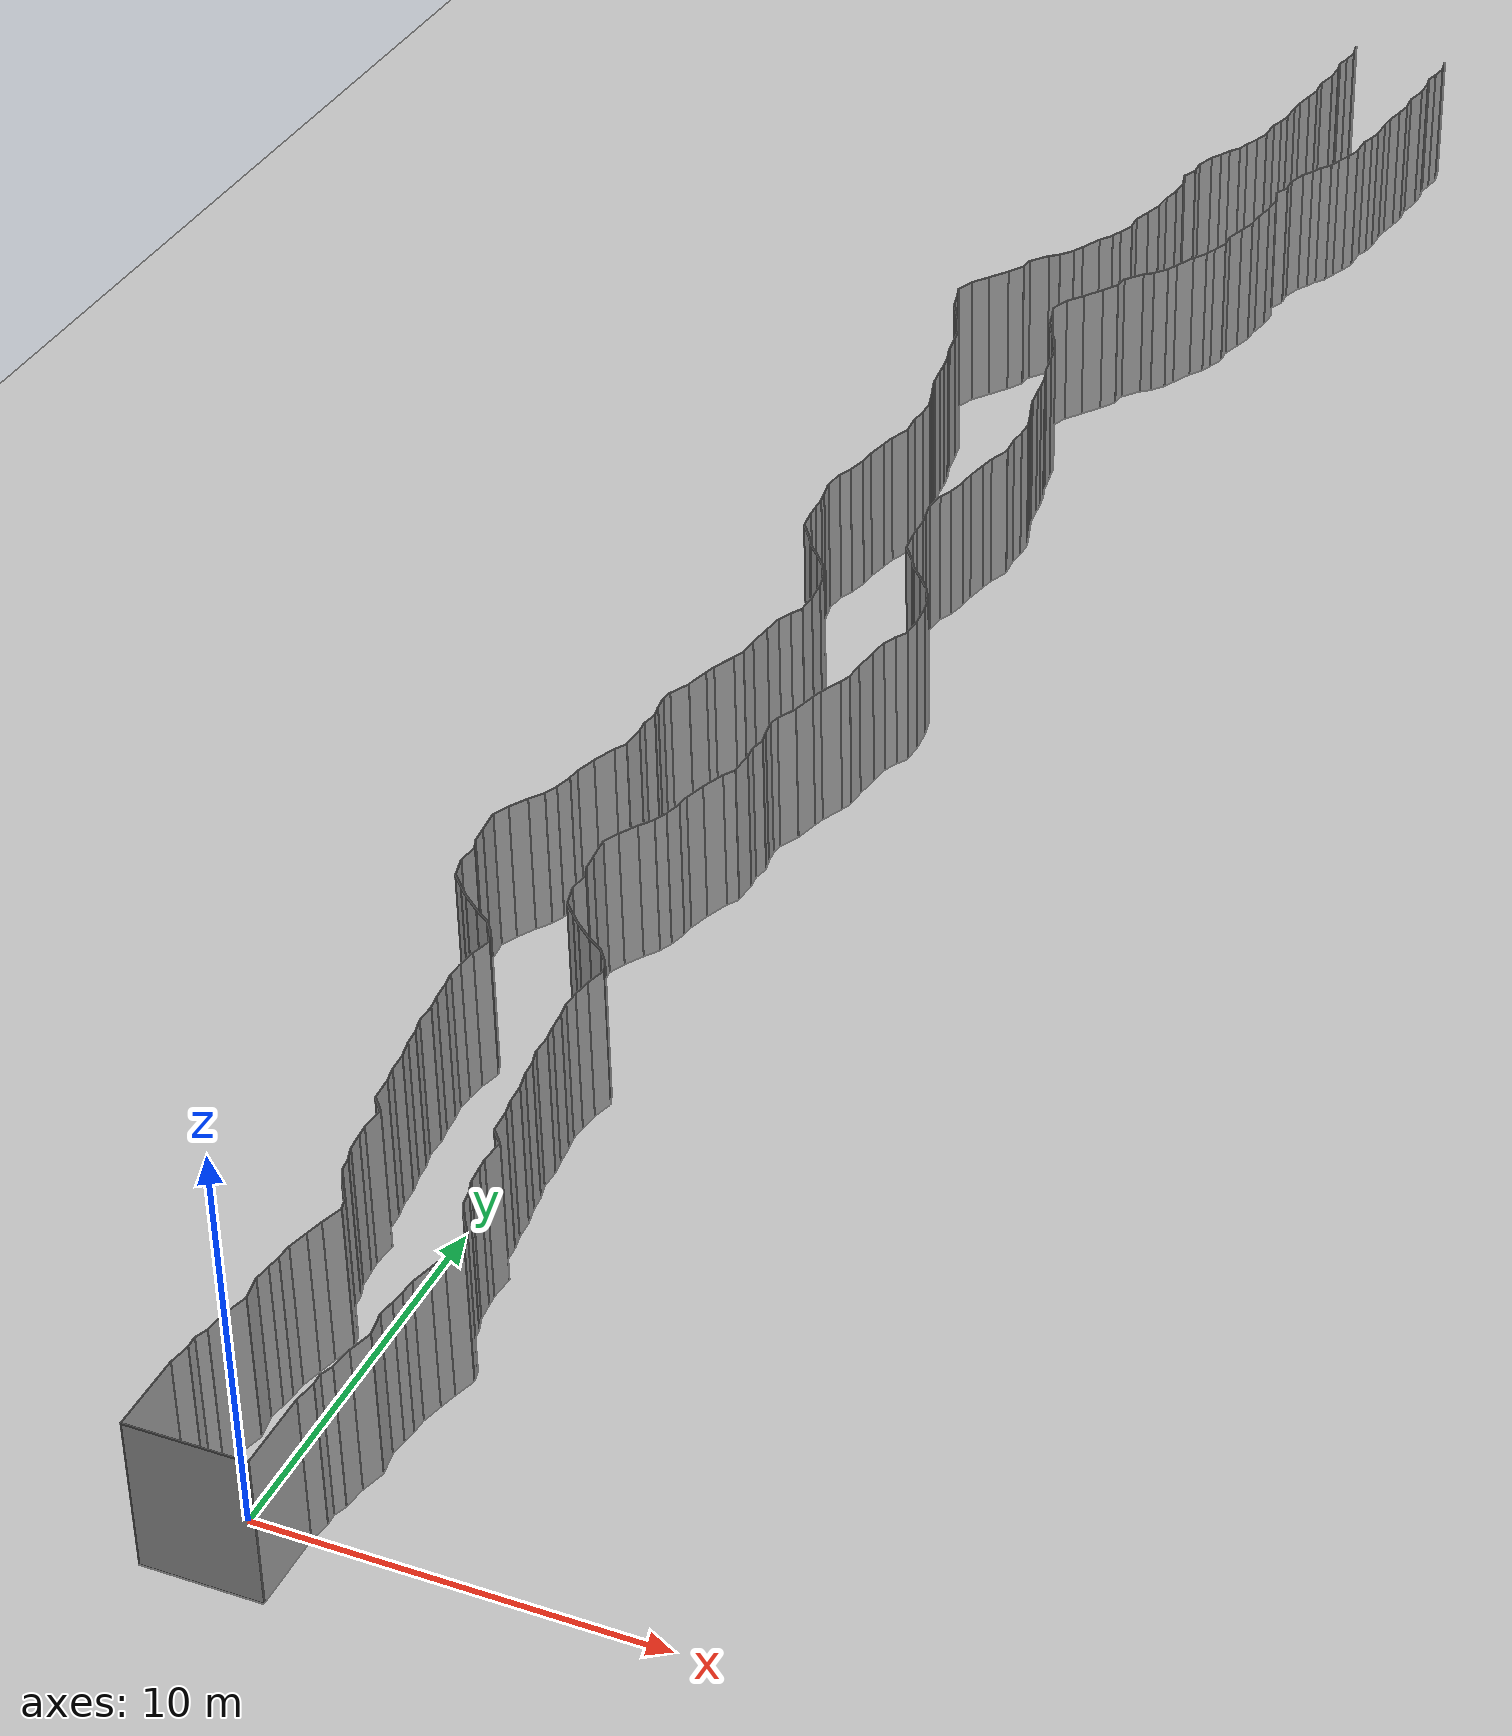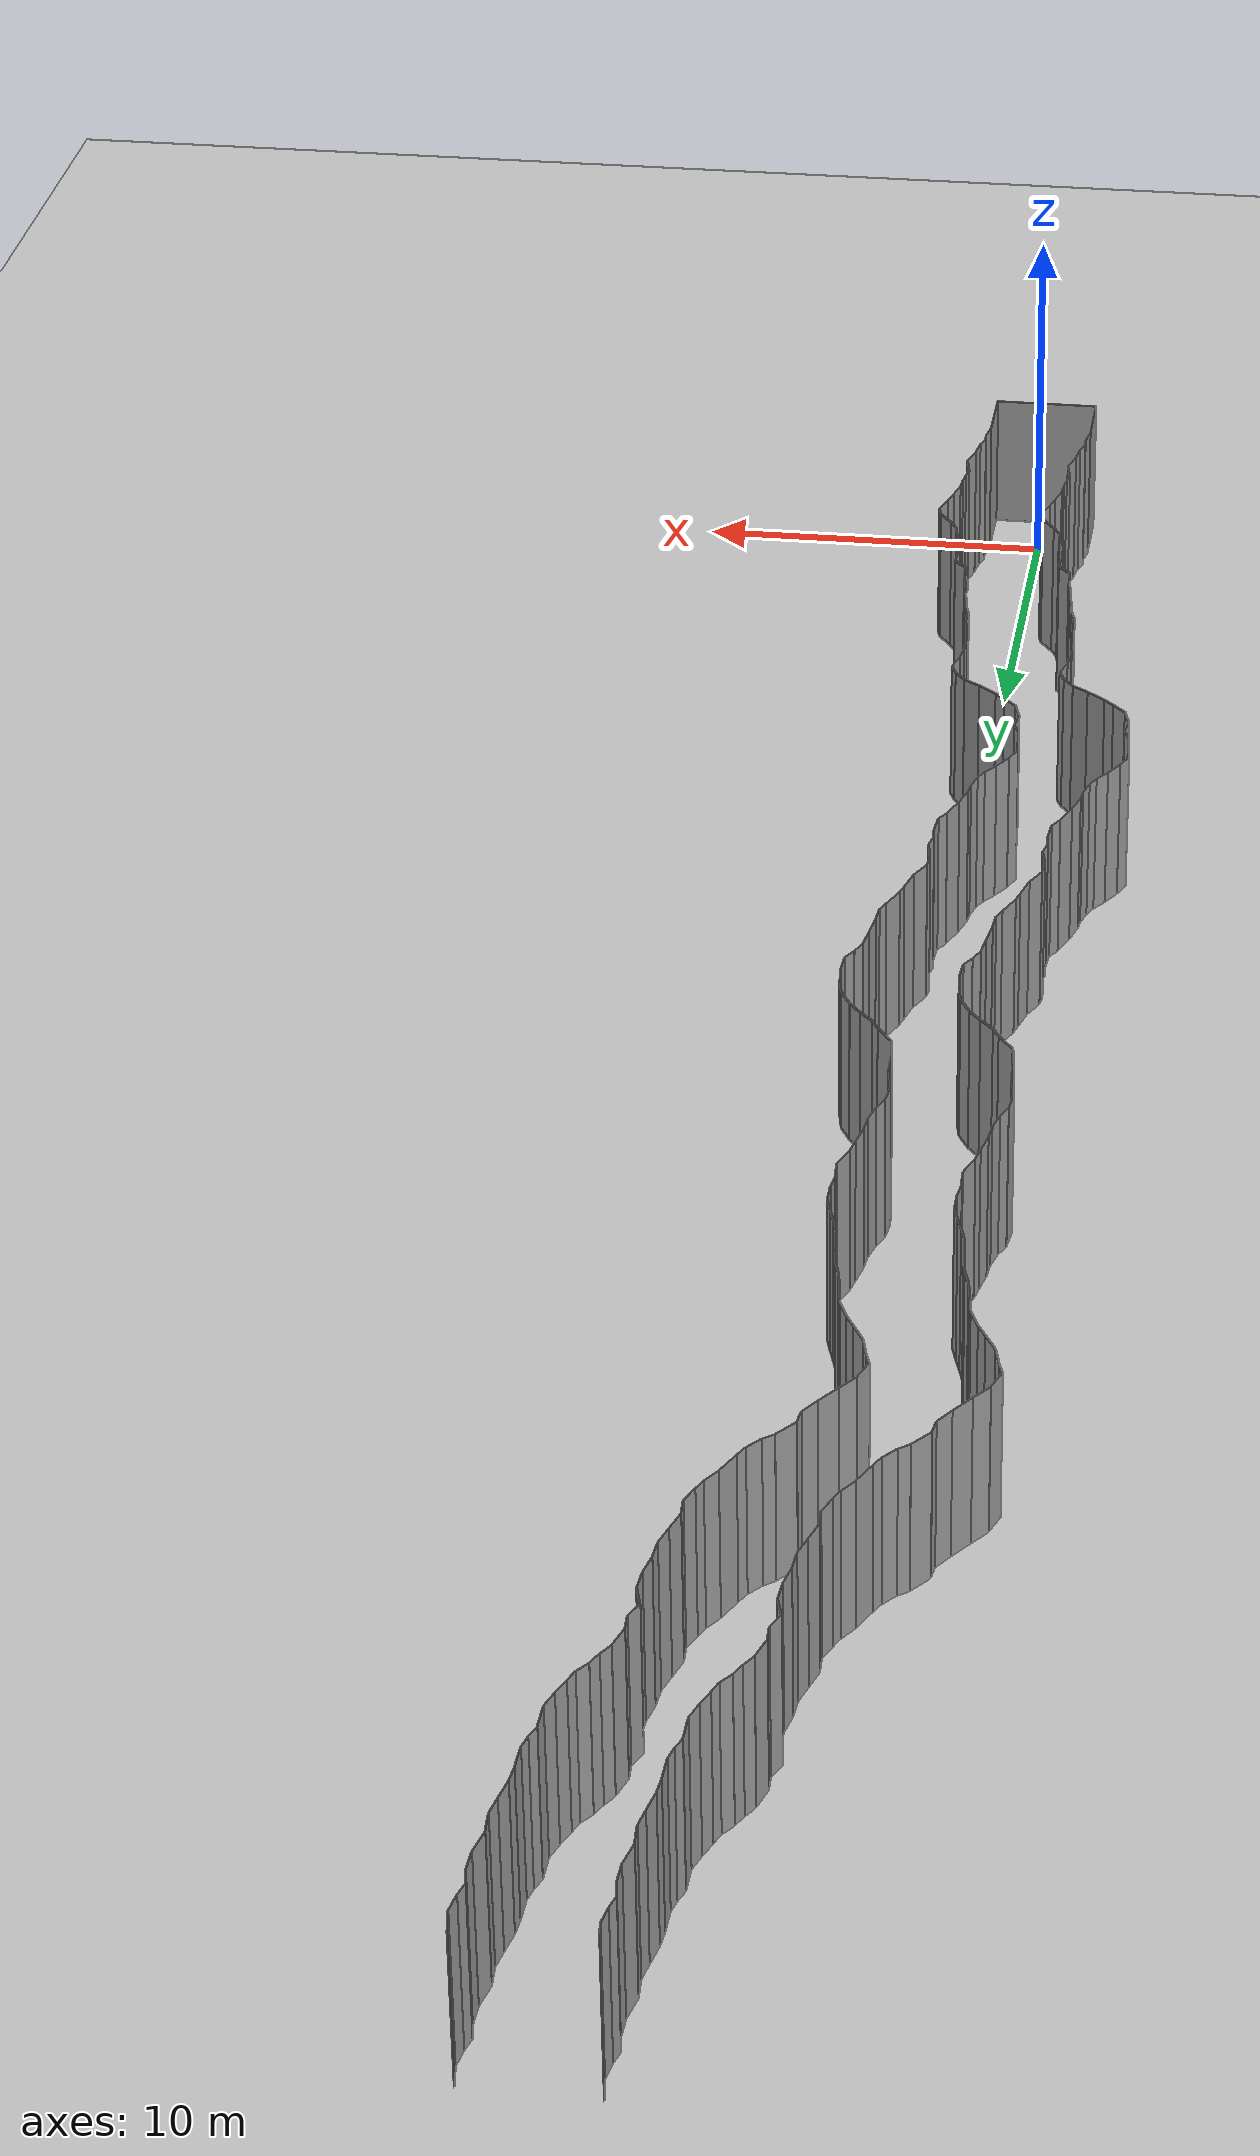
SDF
<sdf version="1.6">
 <world name="default">
  <light name="sun" type="directional">
   <pose>0 0 10 0 -0 0</pose>
   <diffuse>0.8 0.8 0.8 1</diffuse>
   <specular>0.2 0.2 0.2 1</specular>
   <attenuation>
    <range>1000</range>
    <constant>0.9</constant>
    <linear>0.01</linear>
    <quadratic>0.001</quadratic>
   </attenuation>
   <direction>-0.5 0.1 -0.9</direction>
  </light>
  <model name="ground_plane">
   <static>1</static>
   <link name="link">
    <collision name="collision">
     <geometry><plane><normal>0 0 1</normal><size>200 200</size></plane></geometry>
     <surface><friction><ode><mu>100</mu><mu2>50</mu2></ode></friction></surface>
    </collision>
    <visual name="visual">
     <cast_shadows>0</cast_shadows>
     <geometry><plane><normal>0 0 1</normal><size>200 200</size></plane></geometry>
     <material>
      <script><uri>file://media/materials/scripts/gazebo.material</uri><name>Gazebo/Grey</name></script>
     </material>
    </visual>
   </link>
   <pose>0 100 0 0 -0 0</pose>
  </model>
  <gravity>0 0 -9.8</gravity>
  <magnetic_field>6e-06 2.3e-05 -4.2e-05</magnetic_field>
  <atmosphere type="adiabatic"/>
  <physics default="0" name="default_physics" type="ode">
   <max_step_size>0.001</max_step_size>
   <real_time_factor>1</real_time_factor>
   <real_time_update_rate>1000</real_time_update_rate>
  </physics>
  <scene><ambient>0.4 0.4 0.4 1</ambient><background>0.7 0.7 0.7 1</background><shadows>1</shadows></scene>
  <spherical_coordinates>
   <surface_model>EARTH_WGS84</surface_model>
   <latitude_deg>0</latitude_deg>
   <longitude_deg>0</longitude_deg>
   <elevation>0</elevation>
   <heading_deg>0</heading_deg>
  </spherical_coordinates>
  <model name="wall_back">
   <static>1</static>
   <pose>0.0 -2 2 0.0 0 0.0</pose>
   <link name="link">
    <collision name="collision"><geometry><box><size>3 0.02 4</size></box></geometry></collision>
    <visual name="visual">
     <material>
      <script><name>Gazebo/Grey</name><uri>file://media/materials/scripts/gazebo.material</uri></script>
     </material>
     <geometry><box><size>3 0.02 4</size></box></geometry>
    </visual>
   </link>
  </model>
  <model name="wall_left">
   <static>1</static>
   <pose>1.5 -1 2 0 0 0.00</pose>
   <link name="link">
    <collision name="collision"><geometry><box><size>0.02 2 4</size></box></geometry></collision>
    <visual name="visual">
     <material>
      <script><name>Gazebo/Grey</name><uri>file://media/materials/scripts/gazebo.material</uri></script>
     </material>
     <geometry><box><size>0.02 2 4</size></box></geometry>
    </visual>
   </link>
  </model>
  <model name="wall_right">
   <static>1</static>
   <pose>-1.5 -1 2 0 0 0.00</pose>
   <link name="link">
    <collision name="collision"><geometry><box><size>0.02 2 4</size></box></geometry></collision>
    <visual name="visual">
     <material>
      <script><name>Gazebo/Grey</name><uri>file://media/materials/scripts/gazebo.material</uri></script>
     </material>
     <geometry><box><size>0.02 2 4</size></box></geometry>
    </visual>
   </link>
  </model>
  <model name="wall_0">
   <static>1</static>
   <pose>-1.4510614008440241 0.27226961258177046 2 0 0 -0.17784414263756346</pose>
   <link name="link">
    <collision name="collision"><geometry><box><size>0.02 0.553265680927 4</size></box></geometry></collision>
    <visual name="visual">
     <material>
      <script><name>Gazebo/Grey</name><uri>file://media/materials/scripts/gazebo.material</uri></script>
     </material>
     <geometry><box><size>0.02 0.553265680927 4</size></box></geometry>
    </visual>
   </link>
  </model>
  <model name="wall_1">
   <static>1</static>
   <pose>1.5489385991559759 0.27226961258177046 2 0 0 -0.17784414263756346</pose>
   <link name="link">
    <collision name="collision"><geometry><box><size>0.02 0.553265680927 4</size></box></geometry></collision>
    <visual name="visual">
     <material>
      <script><name>Gazebo/Grey</name><uri>file://media/materials/scripts/gazebo.material</uri></script>
     </material>
     <geometry><box><size>0.02 0.553265680927 4</size></box></geometry>
    </visual>
   </link>
  </model>
  <model name="wall_2">
   <static>1</static>
   <pose>-1.4131889546459946 0.7013423824053996 2 0 0 0.0704567162158204</pose>
   <link name="link">
    <collision name="collision"><geometry><box><size>0.02 0.314386321982 4</size></box></geometry></collision>
    <visual name="visual">
     <material>
      <script><name>Gazebo/Grey</name><uri>file://media/materials/scripts/gazebo.material</uri></script>
     </material>
     <geometry><box><size>0.02 0.314386321982 4</size></box></geometry>
    </visual>
   </link>
  </model>
  <model name="wall_3">
   <static>1</static>
   <pose>1.5868110453540054 0.7013423824053996 2 0 0 0.0704567162158204</pose>
   <link name="link">
    <collision name="collision"><geometry><box><size>0.02 0.314386321982 4</size></box></geometry></collision>
    <visual name="visual">
     <material>
      <script><name>Gazebo/Grey</name><uri>file://media/materials/scripts/gazebo.material</uri></script>
     </material>
     <geometry><box><size>0.02 0.314386321982 4</size></box></geometry>
    </visual>
   </link>
  </model>
  <model name="wall_4">
   <static>1</static>
   <pose>-1.360147717933627 1.015774620193739 2 0 0 -0.3862669164413871</pose>
   <link name="link">
    <collision name="collision"><geometry><box><size>0.02 0.340333274566 4</size></box></geometry></collision>
    <visual name="visual">
     <material>
      <script><name>Gazebo/Grey</name><uri>file://media/materials/scripts/gazebo.material</uri></script>
     </material>
     <geometry><box><size>0.02 0.340333274566 4</size></box></geometry>
    </visual>
   </link>
  </model>
  <model name="wall_5">
   <static>1</static>
   <pose>1.639852282066373 1.015774620193739 2 0 0 -0.3862669164413871</pose>
   <link name="link">
    <collision name="collision"><geometry><box><size>0.02 0.340333274566 4</size></box></geometry></collision>
    <visual name="visual">
     <material>
      <script><name>Gazebo/Grey</name><uri>file://media/materials/scripts/gazebo.material</uri></script>
     </material>
     <geometry><box><size>0.02 0.340333274566 4</size></box></geometry>
    </visual>
   </link>
  </model>
  <model name="wall_6">
   <static>1</static>
   <pose>-1.2584821857065456 1.467698916604298 2 0 0 -0.12693447514914025</pose>
   <link name="link">
    <collision name="collision"><geometry><box><size>0.02 0.593364266375 4</size></box></geometry></collision>
    <visual name="visual">
     <material>
      <script><name>Gazebo/Grey</name><uri>file://media/materials/scripts/gazebo.material</uri></script>
     </material>
     <geometry><box><size>0.02 0.593364266375 4</size></box></geometry>
    </visual>
   </link>
  </model>
  <model name="wall_7">
   <static>1</static>
   <pose>1.7415178142934544 1.467698916604298 2 0 0 -0.12693447514914025</pose>
   <link name="link">
    <collision name="collision"><geometry><box><size>0.02 0.593364266375 4</size></box></geometry></collision>
    <visual name="visual">
     <material>
      <script><name>Gazebo/Grey</name><uri>file://media/materials/scripts/gazebo.material</uri></script>
     </material>
     <geometry><box><size>0.02 0.593364266375 4</size></box></geometry>
    </visual>
   </link>
  </model>
  <model name="wall_8">
   <static>1</static>
   <pose>-1.133552409762259 2.0664932754414114 2 0 0 -0.2794284009162872</pose>
   <link name="link">
    <collision name="collision"><geometry><box><size>0.02 0.633572506954 4</size></box></geometry></collision>
    <visual name="visual">
     <material>
      <script><name>Gazebo/Grey</name><uri>file://media/materials/scripts/gazebo.material</uri></script>
     </material>
     <geometry><box><size>0.02 0.633572506954 4</size></box></geometry>
    </visual>
   </link>
  </model>
  <model name="wall_9">
   <static>1</static>
   <pose>1.866447590237741 2.0664932754414114 2 0 0 -0.2794284009162872</pose>
   <link name="link">
    <collision name="collision"><geometry><box><size>0.02 0.633572506954 4</size></box></geometry></collision>
    <visual name="visual">
     <material>
      <script><name>Gazebo/Grey</name><uri>file://media/materials/scripts/gazebo.material</uri></script>
     </material>
     <geometry><box><size>0.02 0.633572506954 4</size></box></geometry>
    </visual>
   </link>
  </model>
  <model name="wall_10">
   <static>1</static>
   <pose>-1.1017332336920902 2.681833785299214 2 0 0 0.17684936663808962</pose>
   <link name="link">
    <collision name="collision"><geometry><box><size>0.02 0.631532836457 4</size></box></geometry></collision>
    <visual name="visual">
     <material>
      <script><name>Gazebo/Grey</name><uri>file://media/materials/scripts/gazebo.material</uri></script>
     </material>
     <geometry><box><size>0.02 0.631532836457 4</size></box></geometry>
    </visual>
   </link>
  </model>
  <model name="wall_11">
   <static>1</static>
   <pose>1.8982667663079098 2.681833785299214 2 0 0 0.17684936663808962</pose>
   <link name="link">
    <collision name="collision"><geometry><box><size>0.02 0.631532836457 4</size></box></geometry></collision>
    <visual name="visual">
     <material>
      <script><name>Gazebo/Grey</name><uri>file://media/materials/scripts/gazebo.material</uri></script>
     </material>
     <geometry><box><size>0.02 0.631532836457 4</size></box></geometry>
    </visual>
   </link>
  </model>
  <model name="wall_12">
   <static>1</static>
   <pose>-1.1270328265631628 3.20628827869749 2 0 0 -0.14068891273038736</pose>
   <link name="link">
    <collision name="collision"><geometry><box><size>0.02 0.431489530005 4</size></box></geometry></collision>
    <visual name="visual">
     <material>
      <script><name>Gazebo/Grey</name><uri>file://media/materials/scripts/gazebo.material</uri></script>
     </material>
     <geometry><box><size>0.02 0.431489530005 4</size></box></geometry>
    </visual>
   </link>
  </model>
  <model name="wall_13">
   <static>1</static>
   <pose>1.8729671734368372 3.20628827869749 2 0 0 -0.14068891273038736</pose>
   <link name="link">
    <collision name="collision"><geometry><box><size>0.02 0.431489530005 4</size></box></geometry></collision>
    <visual name="visual">
     <material>
      <script><name>Gazebo/Grey</name><uri>file://media/materials/scripts/gazebo.material</uri></script>
     </material>
     <geometry><box><size>0.02 0.431489530005 4</size></box></geometry>
    </visual>
   </link>
  </model>
  <model name="wall_14">
   <static>1</static>
   <pose>-1.0712343176284655 3.5970420367363927 2 0 0 -0.14322367572116126</pose>
   <link name="link">
    <collision name="collision"><geometry><box><size>0.02 0.357946271329 4</size></box></geometry></collision>
    <visual name="visual">
     <material>
      <script><name>Gazebo/Grey</name><uri>file://media/materials/scripts/gazebo.material</uri></script>
     </material>
     <geometry><box><size>0.02 0.357946271329 4</size></box></geometry>
    </visual>
   </link>
  </model>
  <model name="wall_15">
   <static>1</static>
   <pose>1.9287656823715345 3.5970420367363927 2 0 0 -0.14322367572116126</pose>
   <link name="link">
    <collision name="collision"><geometry><box><size>0.02 0.357946271329 4</size></box></geometry></collision>
    <visual name="visual">
     <material>
      <script><name>Gazebo/Grey</name><uri>file://media/materials/scripts/gazebo.material</uri></script>
     </material>
     <geometry><box><size>0.02 0.357946271329 4</size></box></geometry>
    </visual>
   </link>
  </model>
  <model name="wall_16">
   <static>1</static>
   <pose>-1.0328271521532806 3.9739733635034153 2 0 0 -0.06428626909097335</pose>
   <link name="link">
    <collision name="collision"><geometry><box><size>0.02 0.400408494551 4</size></box></geometry></collision>
    <visual name="visual">
     <material>
      <script><name>Gazebo/Grey</name><uri>file://media/materials/scripts/gazebo.material</uri></script>
     </material>
     <geometry><box><size>0.02 0.400408494551 4</size></box></geometry>
    </visual>
   </link>
  </model>
  <model name="wall_17">
   <static>1</static>
   <pose>1.9671728478467194 3.9739733635034153 2 0 0 -0.06428626909097335</pose>
   <link name="link">
    <collision name="collision"><geometry><box><size>0.02 0.400408494551 4</size></box></geometry></collision>
    <visual name="visual">
     <material>
      <script><name>Gazebo/Grey</name><uri>file://media/materials/scripts/gazebo.material</uri></script>
     </material>
     <geometry><box><size>0.02 0.400408494551 4</size></box></geometry>
    </visual>
   </link>
  </model>
  <model name="wall_18">
   <static>1</static>
   <pose>-0.9509388020663676 4.439646964082127 2 0 0 -0.25400612948969653</pose>
   <link name="link">
    <collision name="collision"><geometry><box><size>0.02 0.549393929657 4</size></box></geometry></collision>
    <visual name="visual">
     <material>
      <script><name>Gazebo/Grey</name><uri>file://media/materials/scripts/gazebo.material</uri></script>
     </material>
     <geometry><box><size>0.02 0.549393929657 4</size></box></geometry>
    </visual>
   </link>
  </model>
  <model name="wall_19">
   <static>1</static>
   <pose>2.049061197933632 4.439646964082127 2 0 0 -0.25400612948969653</pose>
   <link name="link">
    <collision name="collision"><geometry><box><size>0.02 0.549393929657 4</size></box></geometry></collision>
    <visual name="visual">
     <material>
      <script><name>Gazebo/Grey</name><uri>file://media/materials/scripts/gazebo.material</uri></script>
     </material>
     <geometry><box><size>0.02 0.549393929657 4</size></box></geometry>
    </visual>
   </link>
  </model>
  <model name="wall_20">
   <static>1</static>
   <pose>-0.8212214706037575 4.930960955705222 2 0 0 -0.26298446407842263</pose>
   <link name="link">
    <collision name="collision"><geometry><box><size>0.02 0.46691546019 4</size></box></geometry></collision>
    <visual name="visual">
     <material>
      <script><name>Gazebo/Grey</name><uri>file://media/materials/scripts/gazebo.material</uri></script>
     </material>
     <geometry><box><size>0.02 0.46691546019 4</size></box></geometry>
    </visual>
   </link>
  </model>
  <model name="wall_21">
   <static>1</static>
   <pose>2.1787785293962427 4.930960955705222 2 0 0 -0.26298446407842263</pose>
   <link name="link">
    <collision name="collision"><geometry><box><size>0.02 0.46691546019 4</size></box></geometry></collision>
    <visual name="visual">
     <material>
      <script><name>Gazebo/Grey</name><uri>file://media/materials/scripts/gazebo.material</uri></script>
     </material>
     <geometry><box><size>0.02 0.46691546019 4</size></box></geometry>
    </visual>
   </link>
  </model>
  <model name="wall_22">
   <static>1</static>
   <pose>-0.6699900881126005 5.4388120153842605 2 0 0 -0.3102376020255669</pose>
   <link name="link">
    <collision name="collision"><geometry><box><size>0.02 0.593156614549 4</size></box></geometry></collision>
    <visual name="visual">
     <material>
      <script><name>Gazebo/Grey</name><uri>file://media/materials/scripts/gazebo.material</uri></script>
     </material>
     <geometry><box><size>0.02 0.593156614549 4</size></box></geometry>
    </visual>
   </link>
  </model>
  <model name="wall_23">
   <static>1</static>
   <pose>2.3300099118873994 5.4388120153842605 2 0 0 -0.3102376020255669</pose>
   <link name="link">
    <collision name="collision"><geometry><box><size>0.02 0.593156614549 4</size></box></geometry></collision>
    <visual name="visual">
     <material>
      <script><name>Gazebo/Grey</name><uri>file://media/materials/scripts/gazebo.material</uri></script>
     </material>
     <geometry><box><size>0.02 0.593156614549 4</size></box></geometry>
    </visual>
   </link>
  </model>
  <model name="wall_24">
   <static>1</static>
   <pose>-0.6206682197158915 5.880611606251649 2 0 0 0.2530765057522197</pose>
   <link name="link">
    <collision name="collision"><geometry><box><size>0.02 0.329246833816 4</size></box></geometry></collision>
    <visual name="visual">
     <material>
      <script><name>Gazebo/Grey</name><uri>file://media/materials/scripts/gazebo.material</uri></script>
     </material>
     <geometry><box><size>0.02 0.329246833816 4</size></box></geometry>
    </visual>
   </link>
  </model>
  <model name="wall_25">
   <static>1</static>
   <pose>2.3793317802841085 5.880611606251649 2 0 0 0.2530765057522197</pose>
   <link name="link">
    <collision name="collision"><geometry><box><size>0.02 0.329246833816 4</size></box></geometry></collision>
    <visual name="visual">
     <material>
      <script><name>Gazebo/Grey</name><uri>file://media/materials/scripts/gazebo.material</uri></script>
     </material>
     <geometry><box><size>0.02 0.329246833816 4</size></box></geometry>
    </visual>
   </link>
  </model>
  <model name="wall_26">
   <static>1</static>
   <pose>-0.8430757390639525 6.302089811399908 2 0 0 0.6048625071166142</pose>
   <link name="link">
    <collision name="collision"><geometry><box><size>0.02 0.637259585892 4</size></box></geometry></collision>
    <visual name="visual">
     <material>
      <script><name>Gazebo/Grey</name><uri>file://media/materials/scripts/gazebo.material</uri></script>
     </material>
     <geometry><box><size>0.02 0.637259585892 4</size></box></geometry>
    </visual>
   </link>
  </model>
  <model name="wall_27">
   <static>1</static>
   <pose>2.1569242609360475 6.302089811399908 2 0 0 0.6048625071166142</pose>
   <link name="link">
    <collision name="collision"><geometry><box><size>0.02 0.637259585892 4</size></box></geometry></collision>
    <visual name="visual">
     <material>
      <script><name>Gazebo/Grey</name><uri>file://media/materials/scripts/gazebo.material</uri></script>
     </material>
     <geometry><box><size>0.02 0.637259585892 4</size></box></geometry>
    </visual>
   </link>
  </model>
  <model name="wall_28">
   <static>1</static>
   <pose>-1.1154163347845298 6.733286023980204 2 0 0 0.49439751091214384</pose>
   <link name="link">
    <collision name="collision"><geometry><box><size>0.02 0.38420156124 4</size></box></geometry></collision>
    <visual name="visual">
     <material>
      <script><name>Gazebo/Grey</name><uri>file://media/materials/scripts/gazebo.material</uri></script>
     </material>
     <geometry><box><size>0.02 0.38420156124 4</size></box></geometry>
    </visual>
   </link>
  </model>
  <model name="wall_29">
   <static>1</static>
   <pose>1.8845836652154702 6.733286023980204 2 0 0 0.49439751091214384</pose>
   <link name="link">
    <collision name="collision"><geometry><box><size>0.02 0.38420156124 4</size></box></geometry></collision>
    <visual name="visual">
     <material>
      <script><name>Gazebo/Grey</name><uri>file://media/materials/scripts/gazebo.material</uri></script>
     </material>
     <geometry><box><size>0.02 0.38420156124 4</size></box></geometry>
    </visual>
   </link>
  </model>
  <model name="wall_30">
   <static>1</static>
   <pose>-1.2306127379001681 7.078196218832997 2 0 0 0.1359178704899804</pose>
   <link name="link">
    <collision name="collision"><geometry><box><size>0.02 0.354898232374 4</size></box></geometry></collision>
    <visual name="visual">
     <material>
      <script><name>Gazebo/Grey</name><uri>file://media/materials/scripts/gazebo.material</uri></script>
     </material>
     <geometry><box><size>0.02 0.354898232374 4</size></box></geometry>
    </visual>
   </link>
  </model>
  <model name="wall_31">
   <static>1</static>
   <pose>1.7693872620998319 7.078196218832997 2 0 0 0.1359178704899804</pose>
   <link name="link">
    <collision name="collision"><geometry><box><size>0.02 0.354898232374 4</size></box></geometry></collision>
    <visual name="visual">
     <material>
      <script><name>Gazebo/Grey</name><uri>file://media/materials/scripts/gazebo.material</uri></script>
     </material>
     <geometry><box><size>0.02 0.354898232374 4</size></box></geometry>
    </visual>
   </link>
  </model>
  <model name="wall_32">
   <static>1</static>
   <pose>-1.3182803285968272 7.4312952756271065 2 0 0 0.3445572357663062</pose>
   <link name="link">
    <collision name="collision"><geometry><box><size>0.02 0.376714319493 4</size></box></geometry></collision>
    <visual name="visual">
     <material>
      <script><name>Gazebo/Grey</name><uri>file://media/materials/scripts/gazebo.material</uri></script>
     </material>
     <geometry><box><size>0.02 0.376714319493 4</size></box></geometry>
    </visual>
   </link>
  </model>
  <model name="wall_33">
   <static>1</static>
   <pose>1.6817196714031728 7.4312952756271065 2 0 0 0.3445572357663062</pose>
   <link name="link">
    <collision name="collision"><geometry><box><size>0.02 0.376714319493 4</size></box></geometry></collision>
    <visual name="visual">
     <material>
      <script><name>Gazebo/Grey</name><uri>file://media/materials/scripts/gazebo.material</uri></script>
     </material>
     <geometry><box><size>0.02 0.376714319493 4</size></box></geometry>
    </visual>
   </link>
  </model>
  <model name="wall_34">
   <static>1</static>
   <pose>-1.4061348706168952 7.847483247230103 2 0 0 0.10108217442688737</pose>
   <link name="link">
    <collision name="collision"><geometry><box><size>0.02 0.480254406274 4</size></box></geometry></collision>
    <visual name="visual">
     <material>
      <script><name>Gazebo/Grey</name><uri>file://media/materials/scripts/gazebo.material</uri></script>
     </material>
     <geometry><box><size>0.02 0.480254406274 4</size></box></geometry>
    </visual>
   </link>
  </model>
  <model name="wall_35">
   <static>1</static>
   <pose>1.5938651293831048 7.847483247230103 2 0 0 0.10108217442688737</pose>
   <link name="link">
    <collision name="collision"><geometry><box><size>0.02 0.480254406274 4</size></box></geometry></collision>
    <visual name="visual">
     <material>
      <script><name>Gazebo/Grey</name><uri>file://media/materials/scripts/gazebo.material</uri></script>
     </material>
     <geometry><box><size>0.02 0.480254406274 4</size></box></geometry>
    </visual>
   </link>
  </model>
  <model name="wall_36">
   <static>1</static>
   <pose>-1.4426236268751231 8.239152183468175 2 0 0 0.08006474513999451</pose>
   <link name="link">
    <collision name="collision"><geometry><box><size>0.02 0.306516820366 4</size></box></geometry></collision>
    <visual name="visual">
     <material>
      <script><name>Gazebo/Grey</name><uri>file://media/materials/scripts/gazebo.material</uri></script>
     </material>
     <geometry><box><size>0.02 0.306516820366 4</size></box></geometry>
    </visual>
   </link>
  </model>
  <model name="wall_37">
   <static>1</static>
   <pose>1.5573763731248769 8.239152183468175 2 0 0 0.08006474513999451</pose>
   <link name="link">
    <collision name="collision"><geometry><box><size>0.02 0.306516820366 4</size></box></geometry></collision>
    <visual name="visual">
     <material>
      <script><name>Gazebo/Grey</name><uri>file://media/materials/scripts/gazebo.material</uri></script>
     </material>
     <geometry><box><size>0.02 0.306516820366 4</size></box></geometry>
    </visual>
   </link>
  </model>
  <model name="wall_38">
   <static>1</static>
   <pose>-1.4296244603228077 8.718072273795189 2 0 0 -0.07728391278805666</pose>
   <link name="link">
    <collision name="collision"><geometry><box><size>0.02 0.654258183048 4</size></box></geometry></collision>
    <visual name="visual">
     <material>
      <script><name>Gazebo/Grey</name><uri>file://media/materials/scripts/gazebo.material</uri></script>
     </material>
     <geometry><box><size>0.02 0.654258183048 4</size></box></geometry>
    </visual>
   </link>
  </model>
  <model name="wall_39">
   <static>1</static>
   <pose>1.5703755396771923 8.718072273795189 2 0 0 -0.07728391278805666</pose>
   <link name="link">
    <collision name="collision"><geometry><box><size>0.02 0.654258183048 4</size></box></geometry></collision>
    <visual name="visual">
     <material>
      <script><name>Gazebo/Grey</name><uri>file://media/materials/scripts/gazebo.material</uri></script>
     </material>
     <geometry><box><size>0.02 0.654258183048 4</size></box></geometry>
    </visual>
   </link>
  </model>
  <model name="wall_40">
   <static>1</static>
   <pose>-1.5703119641842869 9.233145682015286 2 0 0 0.7207409379286189</pose>
   <link name="link">
    <collision name="collision"><geometry><box><size>0.02 0.502905643045 4</size></box></geometry></collision>
    <visual name="visual">
     <material>
      <script><name>Gazebo/Grey</name><uri>file://media/materials/scripts/gazebo.material</uri></script>
     </material>
     <geometry><box><size>0.02 0.502905643045 4</size></box></geometry>
    </visual>
   </link>
  </model>
  <model name="wall_41">
   <static>1</static>
   <pose>1.4296880358157131 9.233145682015286 2 0 0 0.7207409379286189</pose>
   <link name="link">
    <collision name="collision"><geometry><box><size>0.02 0.502905643045 4</size></box></geometry></collision>
    <visual name="visual">
     <material>
      <script><name>Gazebo/Grey</name><uri>file://media/materials/scripts/gazebo.material</uri></script>
     </material>
     <geometry><box><size>0.02 0.502905643045 4</size></box></geometry>
    </visual>
   </link>
  </model>
  <model name="wall_42">
   <static>1</static>
   <pose>-1.7563336963715983 9.73940504404195 2 0 0 0.06318439311915218</pose>
   <link name="link">
    <collision name="collision"><geometry><box><size>0.02 0.635946196708 4</size></box></geometry></collision>
    <visual name="visual">
     <material>
      <script><name>Gazebo/Grey</name><uri>file://media/materials/scripts/gazebo.material</uri></script>
     </material>
     <geometry><box><size>0.02 0.635946196708 4</size></box></geometry>
    </visual>
   </link>
  </model>
  <model name="wall_43">
   <static>1</static>
   <pose>1.2436663036284017 9.73940504404195 2 0 0 0.06318439311915218</pose>
   <link name="link">
    <collision name="collision"><geometry><box><size>0.02 0.635946196708 4</size></box></geometry></collision>
    <visual name="visual">
     <material>
      <script><name>Gazebo/Grey</name><uri>file://media/materials/scripts/gazebo.material</uri></script>
     </material>
     <geometry><box><size>0.02 0.635946196708 4</size></box></geometry>
    </visual>
   </link>
  </model>
  <model name="wall_44">
   <static>1</static>
   <pose>-1.8194577117034247 10.259236486240194 2 0 0 0.2094643616543292</pose>
   <link name="link">
    <collision name="collision"><geometry><box><size>0.02 0.414035507725 4</size></box></geometry></collision>
    <visual name="visual">
     <material>
      <script><name>Gazebo/Grey</name><uri>file://media/materials/scripts/gazebo.material</uri></script>
     </material>
     <geometry><box><size>0.02 0.414035507725 4</size></box></geometry>
    </visual>
   </link>
  </model>
  <model name="wall_45">
   <static>1</static>
   <pose>1.1805422882965753 10.259236486240194 2 0 0 0.2094643616543292</pose>
   <link name="link">
    <collision name="collision"><geometry><box><size>0.02 0.414035507725 4</size></box></geometry></collision>
    <visual name="visual">
     <material>
      <script><name>Gazebo/Grey</name><uri>file://media/materials/scripts/gazebo.material</uri></script>
     </material>
     <geometry><box><size>0.02 0.414035507725 4</size></box></geometry>
    </visual>
   </link>
  </model>
  <model name="wall_46">
   <static>1</static>
   <pose>-1.875421869682316 10.7203639757701 2 0 0 0.049904332648089626</pose>
   <link name="link">
    <collision name="collision"><geometry><box><size>0.02 0.517914063708 4</size></box></geometry></collision>
    <visual name="visual">
     <material>
      <script><name>Gazebo/Grey</name><uri>file://media/materials/scripts/gazebo.material</uri></script>
     </material>
     <geometry><box><size>0.02 0.517914063708 4</size></box></geometry>
    </visual>
   </link>
  </model>
  <model name="wall_47">
   <static>1</static>
   <pose>1.124578130317684 10.7203639757701 2 0 0 0.049904332648089626</pose>
   <link name="link">
    <collision name="collision"><geometry><box><size>0.02 0.517914063708 4</size></box></geometry></collision>
    <visual name="visual">
     <material>
      <script><name>Gazebo/Grey</name><uri>file://media/materials/scripts/gazebo.material</uri></script>
     </material>
     <geometry><box><size>0.02 0.517914063708 4</size></box></geometry>
    </visual>
   </link>
  </model>
  <model name="wall_48">
   <static>1</static>
   <pose>-1.942731686995152 11.219851072159386 2 0 0 0.22210585862176607</pose>
   <link name="link">
    <collision name="collision"><geometry><box><size>0.02 0.493835626928 4</size></box></geometry></collision>
    <visual name="visual">
     <material>
      <script><name>Gazebo/Grey</name><uri>file://media/materials/scripts/gazebo.material</uri></script>
     </material>
     <geometry><box><size>0.02 0.493835626928 4</size></box></geometry>
    </visual>
   </link>
  </model>
  <model name="wall_49">
   <static>1</static>
   <pose>1.057268313004848 11.219851072159386 2 0 0 0.22210585862176607</pose>
   <link name="link">
    <collision name="collision"><geometry><box><size>0.02 0.493835626928 4</size></box></geometry></collision>
    <visual name="visual">
     <material>
      <script><name>Gazebo/Grey</name><uri>file://media/materials/scripts/gazebo.material</uri></script>
     </material>
     <geometry><box><size>0.02 0.493835626928 4</size></box></geometry>
    </visual>
   </link>
  </model>
  <model name="wall_50">
   <static>1</static>
   <pose>-2.013806907833596 11.672866145919334 2 0 0 0.07847216417222873</pose>
   <link name="link">
    <collision name="collision"><geometry><box><size>0.02 0.425635067301 4</size></box></geometry></collision>
    <visual name="visual">
     <material>
      <script><name>Gazebo/Grey</name><uri>file://media/materials/scripts/gazebo.material</uri></script>
     </material>
     <geometry><box><size>0.02 0.425635067301 4</size></box></geometry>
    </visual>
   </link>
  </model>
  <model name="wall_51">
   <static>1</static>
   <pose>0.9861930921664039 11.672866145919334 2 0 0 0.07847216417222873</pose>
   <link name="link">
    <collision name="collision"><geometry><box><size>0.02 0.425635067301 4</size></box></geometry></collision>
    <visual name="visual">
     <material>
      <script><name>Gazebo/Grey</name><uri>file://media/materials/scripts/gazebo.material</uri></script>
     </material>
     <geometry><box><size>0.02 0.425635067301 4</size></box></geometry>
    </visual>
   </link>
  </model>
  <model name="wall_52">
   <static>1</static>
   <pose>-2.084917750806969 12.089637878632406 2 0 0 0.25998764255612705</pose>
   <link name="link">
    <collision name="collision"><geometry><box><size>0.02 0.423449016207 4</size></box></geometry></collision>
    <visual name="visual">
     <material>
      <script><name>Gazebo/Grey</name><uri>file://media/materials/scripts/gazebo.material</uri></script>
     </material>
     <geometry><box><size>0.02 0.423449016207 4</size></box></geometry>
    </visual>
   </link>
  </model>
  <model name="wall_53">
   <static>1</static>
   <pose>0.915082249193031 12.089637878632406 2 0 0 0.25998764255612705</pose>
   <link name="link">
    <collision name="collision"><geometry><box><size>0.02 0.423449016207 4</size></box></geometry></collision>
    <visual name="visual">
     <material>
      <script><name>Gazebo/Grey</name><uri>file://media/materials/scripts/gazebo.material</uri></script>
     </material>
     <geometry><box><size>0.02 0.423449016207 4</size></box></geometry>
    </visual>
   </link>
  </model>
  <model name="wall_54">
   <static>1</static>
   <pose>-2.1308924688883764 12.56192897705406 2 0 0 -0.03156805198859444</pose>
   <link name="link">
    <collision name="collision"><geometry><box><size>0.02 0.535630833246 4</size></box></geometry></collision>
    <visual name="visual">
     <material>
      <script><name>Gazebo/Grey</name><uri>file://media/materials/scripts/gazebo.material</uri></script>
     </material>
     <geometry><box><size>0.02 0.535630833246 4</size></box></geometry>
    </visual>
   </link>
  </model>
  <model name="wall_55">
   <static>1</static>
   <pose>0.8691075311116236 12.56192897705406 2 0 0 -0.03156805198859444</pose>
   <link name="link">
    <collision name="collision"><geometry><box><size>0.02 0.535630833246 4</size></box></geometry></collision>
    <visual name="visual">
     <material>
      <script><name>Gazebo/Grey</name><uri>file://media/materials/scripts/gazebo.material</uri></script>
     </material>
     <geometry><box><size>0.02 0.535630833246 4</size></box></geometry>
    </visual>
   </link>
  </model>
  <model name="wall_56">
   <static>1</static>
   <pose>-2.154161942373587 13.030462414617539 2 0 0 0.1566460467573428</pose>
   <link name="link">
    <collision name="collision"><geometry><box><size>0.02 0.406682296322 4</size></box></geometry></collision>
    <visual name="visual">
     <material>
      <script><name>Gazebo/Grey</name><uri>file://media/materials/scripts/gazebo.material</uri></script>
     </material>
     <geometry><box><size>0.02 0.406682296322 4</size></box></geometry>
    </visual>
   </link>
  </model>
  <model name="wall_57">
   <static>1</static>
   <pose>0.8458380576264131 13.030462414617539 2 0 0 0.1566460467573428</pose>
   <link name="link">
    <collision name="collision"><geometry><box><size>0.02 0.406682296322 4</size></box></geometry></collision>
    <visual name="visual">
     <material>
      <script><name>Gazebo/Grey</name><uri>file://media/materials/scripts/gazebo.material</uri></script>
     </material>
     <geometry><box><size>0.02 0.406682296322 4</size></box></geometry>
    </visual>
   </link>
  </model>
  <model name="wall_58">
   <static>1</static>
   <pose>-2.2064051174617987 13.487109349726365 2 0 0 0.0800516176216397</pose>
   <link name="link">
    <collision name="collision"><geometry><box><size>0.02 0.51323455383 4</size></box></geometry></collision>
    <visual name="visual">
     <material>
      <script><name>Gazebo/Grey</name><uri>file://media/materials/scripts/gazebo.material</uri></script>
     </material>
     <geometry><box><size>0.02 0.51323455383 4</size></box></geometry>
    </visual>
   </link>
  </model>
  <model name="wall_59">
   <static>1</static>
   <pose>0.7935948825382013 13.487109349726365 2 0 0 0.0800516176216397</pose>
   <link name="link">
    <collision name="collision"><geometry><box><size>0.02 0.51323455383 4</size></box></geometry></collision>
    <visual name="visual">
     <material>
      <script><name>Gazebo/Grey</name><uri>file://media/materials/scripts/gazebo.material</uri></script>
     </material>
     <geometry><box><size>0.02 0.51323455383 4</size></box></geometry>
    </visual>
   </link>
  </model>
  <model name="wall_60">
   <static>1</static>
   <pose>-2.2584367095775075 13.939643765363027 2 0 0 0.15881715963549048</pose>
   <link name="link">
    <collision name="collision"><geometry><box><size>0.02 0.398492886814 4</size></box></geometry></collision>
    <visual name="visual">
     <material>
      <script><name>Gazebo/Grey</name><uri>file://media/materials/scripts/gazebo.material</uri></script>
     </material>
     <geometry><box><size>0.02 0.398492886814 4</size></box></geometry>
    </visual>
   </link>
  </model>
  <model name="wall_61">
   <static>1</static>
   <pose>0.7415632904224925 13.939643765363027 2 0 0 0.15881715963549048</pose>
   <link name="link">
    <collision name="collision"><geometry><box><size>0.02 0.398492886814 4</size></box></geometry></collision>
    <visual name="visual">
     <material>
      <script><name>Gazebo/Grey</name><uri>file://media/materials/scripts/gazebo.material</uri></script>
     </material>
     <geometry><box><size>0.02 0.398492886814 4</size></box></geometry>
    </visual>
   </link>
  </model>
  <model name="wall_62">
   <static>1</static>
   <pose>-2.273502406085278 14.346934054915321 2 0 0 -0.07794716738088803</pose>
   <link name="link">
    <collision name="collision"><geometry><box><size>0.02 0.422385215286 4</size></box></geometry></collision>
    <visual name="visual">
     <material>
      <script><name>Gazebo/Grey</name><uri>file://media/materials/scripts/gazebo.material</uri></script>
     </material>
     <geometry><box><size>0.02 0.422385215286 4</size></box></geometry>
    </visual>
   </link>
  </model>
  <model name="wall_63">
   <static>1</static>
   <pose>0.726497593914722 14.346934054915321 2 0 0 -0.07794716738088803</pose>
   <link name="link">
    <collision name="collision"><geometry><box><size>0.02 0.422385215286 4</size></box></geometry></collision>
    <visual name="visual">
     <material>
      <script><name>Gazebo/Grey</name><uri>file://media/materials/scripts/gazebo.material</uri></script>
     </material>
     <geometry><box><size>0.02 0.422385215286 4</size></box></geometry>
    </visual>
   </link>
  </model>
  <model name="wall_64">
   <static>1</static>
   <pose>-2.2248271673228044 14.81456398776168 2 0 0 -0.12471965528714725</pose>
   <link name="link">
    <collision name="collision"><geometry><box><size>0.02 0.518182094539 4</size></box></geometry></collision>
    <visual name="visual">
     <material>
      <script><name>Gazebo/Grey</name><uri>file://media/materials/scripts/gazebo.material</uri></script>
     </material>
     <geometry><box><size>0.02 0.518182094539 4</size></box></geometry>
    </visual>
   </link>
  </model>
  <model name="wall_65">
   <static>1</static>
   <pose>0.7751728326771956 14.81456398776168 2 0 0 -0.12471965528714725</pose>
   <link name="link">
    <collision name="collision"><geometry><box><size>0.02 0.518182094539 4</size></box></geometry></collision>
    <visual name="visual">
     <material>
      <script><name>Gazebo/Grey</name><uri>file://media/materials/scripts/gazebo.material</uri></script>
     </material>
     <geometry><box><size>0.02 0.518182094539 4</size></box></geometry>
    </visual>
   </link>
  </model>
  <model name="wall_66">
   <static>1</static>
   <pose>-2.1158525231552496 15.345142546608834 2 0 0 -0.2735667307128934</pose>
   <link name="link">
    <collision name="collision"><geometry><box><size>0.02 0.568126654679 4</size></box></geometry></collision>
    <visual name="visual">
     <material>
      <script><name>Gazebo/Grey</name><uri>file://media/materials/scripts/gazebo.material</uri></script>
     </material>
     <geometry><box><size>0.02 0.568126654679 4</size></box></geometry>
    </visual>
   </link>
  </model>
  <model name="wall_67">
   <static>1</static>
   <pose>0.8841474768447504 15.345142546608834 2 0 0 -0.2735667307128934</pose>
   <link name="link">
    <collision name="collision"><geometry><box><size>0.02 0.568126654679 4</size></box></geometry></collision>
    <visual name="visual">
     <material>
      <script><name>Gazebo/Grey</name><uri>file://media/materials/scripts/gazebo.material</uri></script>
     </material>
     <geometry><box><size>0.02 0.568126654679 4</size></box></geometry>
    </visual>
   </link>
  </model>
  <model name="wall_68">
   <static>1</static>
   <pose>-2.1128247132251623 15.796494428916368 2 0 0 0.3929300302445417</pose>
   <link name="link">
    <collision name="collision"><geometry><box><size>0.02 0.385047867322 4</size></box></geometry></collision>
    <visual name="visual">
     <material>
      <script><name>Gazebo/Grey</name><uri>file://media/materials/scripts/gazebo.material</uri></script>
     </material>
     <geometry><box><size>0.02 0.385047867322 4</size></box></geometry>
    </visual>
   </link>
  </model>
  <model name="wall_69">
   <static>1</static>
   <pose>0.8871752867748377 15.796494428916368 2 0 0 0.3929300302445417</pose>
   <link name="link">
    <collision name="collision"><geometry><box><size>0.02 0.385047867322 4</size></box></geometry></collision>
    <visual name="visual">
     <material>
      <script><name>Gazebo/Grey</name><uri>file://media/materials/scripts/gazebo.material</uri></script>
     </material>
     <geometry><box><size>0.02 0.385047867322 4</size></box></geometry>
    </visual>
   </link>
  </model>
  <model name="wall_70">
   <static>1</static>
   <pose>-2.3271195613443876 16.157484691660088 2 0 0 0.6546738767870675</pose>
   <link name="link">
    <collision name="collision"><geometry><box><size>0.02 0.461743859274 4</size></box></geometry></collision>
    <visual name="visual">
     <material>
      <script><name>Gazebo/Grey</name><uri>file://media/materials/scripts/gazebo.material</uri></script>
     </material>
     <geometry><box><size>0.02 0.461743859274 4</size></box></geometry>
    </visual>
   </link>
  </model>
  <model name="wall_71">
   <static>1</static>
   <pose>0.6728804386556124 16.157484691660088 2 0 0 0.6546738767870675</pose>
   <link name="link">
    <collision name="collision"><geometry><box><size>0.02 0.461743859274 4</size></box></geometry></collision>
    <visual name="visual">
     <material>
      <script><name>Gazebo/Grey</name><uri>file://media/materials/scripts/gazebo.material</uri></script>
     </material>
     <geometry><box><size>0.02 0.461743859274 4</size></box></geometry>
    </visual>
   </link>
  </model>
  <model name="wall_72">
   <static>1</static>
   <pose>-2.686708989568177 16.49051149660358 2 0 0 0.9706262165268534</pose>
   <link name="link">
    <collision name="collision"><geometry><box><size>0.02 0.530782549284 4</size></box></geometry></collision>
    <visual name="visual">
     <material>
      <script><name>Gazebo/Grey</name><uri>file://media/materials/scripts/gazebo.material</uri></script>
     </material>
     <geometry><box><size>0.02 0.530782549284 4</size></box></geometry>
    </visual>
   </link>
  </model>
  <model name="wall_73">
   <static>1</static>
   <pose>0.31329101043182295 16.49051149660358 2 0 0 0.9706262165268534</pose>
   <link name="link">
    <collision name="collision"><geometry><box><size>0.02 0.530782549284 4</size></box></geometry></collision>
    <visual name="visual">
     <material>
      <script><name>Gazebo/Grey</name><uri>file://media/materials/scripts/gazebo.material</uri></script>
     </material>
     <geometry><box><size>0.02 0.530782549284 4</size></box></geometry>
    </visual>
   </link>
  </model>
  <model name="wall_74">
   <static>1</static>
   <pose>-3.157199100774008 16.85156726297024 2 0 0 0.8723109527861052</pose>
   <link name="link">
    <collision name="collision"><geometry><box><size>0.02 0.656759292511 4</size></box></geometry></collision>
    <visual name="visual">
     <material>
      <script><name>Gazebo/Grey</name><uri>file://media/materials/scripts/gazebo.material</uri></script>
     </material>
     <geometry><box><size>0.02 0.656759292511 4</size></box></geometry>
    </visual>
   </link>
  </model>
  <model name="wall_75">
   <static>1</static>
   <pose>-0.15719910077400812 16.85156726297024 2 0 0 0.8723109527861052</pose>
   <link name="link">
    <collision name="collision"><geometry><box><size>0.02 0.656759292511 4</size></box></geometry></collision>
    <visual name="visual">
     <material>
      <script><name>Gazebo/Grey</name><uri>file://media/materials/scripts/gazebo.material</uri></script>
     </material>
     <geometry><box><size>0.02 0.656759292511 4</size></box></geometry>
    </visual>
   </link>
  </model>
  <model name="wall_76">
   <static>1</static>
   <pose>-3.5410019303740015 17.194973606267954 2 0 0 0.785719727233147</pose>
   <link name="link">
    <collision name="collision"><geometry><box><size>0.02 0.37414876576 4</size></box></geometry></collision>
    <visual name="visual">
     <material>
      <script><name>Gazebo/Grey</name><uri>file://media/materials/scripts/gazebo.material</uri></script>
     </material>
     <geometry><box><size>0.02 0.37414876576 4</size></box></geometry>
    </visual>
   </link>
  </model>
  <model name="wall_77">
   <static>1</static>
   <pose>-0.5410019303740015 17.194973606267954 2 0 0 0.785719727233147</pose>
   <link name="link">
    <collision name="collision"><geometry><box><size>0.02 0.37414876576 4</size></box></geometry></collision>
    <visual name="visual">
     <material>
      <script><name>Gazebo/Grey</name><uri>file://media/materials/scripts/gazebo.material</uri></script>
     </material>
     <geometry><box><size>0.02 0.37414876576 4</size></box></geometry>
    </visual>
   </link>
  </model>
  <model name="wall_78">
   <static>1</static>
   <pose>-3.846775899688538 17.514674699610165 2 0 0 0.7465932302845639</pose>
   <link name="link">
    <collision name="collision"><geometry><box><size>0.02 0.510791102315 4</size></box></geometry></collision>
    <visual name="visual">
     <material>
      <script><name>Gazebo/Grey</name><uri>file://media/materials/scripts/gazebo.material</uri></script>
     </material>
     <geometry><box><size>0.02 0.510791102315 4</size></box></geometry>
    </visual>
   </link>
  </model>
  <model name="wall_79">
   <static>1</static>
   <pose>-0.846775899688538 17.514674699610165 2 0 0 0.7465932302845639</pose>
   <link name="link">
    <collision name="collision"><geometry><box><size>0.02 0.510791102315 4</size></box></geometry></collision>
    <visual name="visual">
     <material>
      <script><name>Gazebo/Grey</name><uri>file://media/materials/scripts/gazebo.material</uri></script>
     </material>
     <geometry><box><size>0.02 0.510791102315 4</size></box></geometry>
    </visual>
   </link>
  </model>
  <model name="wall_80">
   <static>1</static>
   <pose>-4.097035900784917 17.9949265951174 2 0 0 0.25655750265288335</pose>
   <link name="link">
    <collision name="collision"><geometry><box><size>0.02 0.605394668137 4</size></box></geometry></collision>
    <visual name="visual">
     <material>
      <script><name>Gazebo/Grey</name><uri>file://media/materials/scripts/gazebo.material</uri></script>
     </material>
     <geometry><box><size>0.02 0.605394668137 4</size></box></geometry>
    </visual>
   </link>
  </model>
  <model name="wall_81">
   <static>1</static>
   <pose>-1.0970359007849169 17.9949265951174 2 0 0 0.25655750265288335</pose>
   <link name="link">
    <collision name="collision"><geometry><box><size>0.02 0.605394668137 4</size></box></geometry></collision>
    <visual name="visual">
     <material>
      <script><name>Gazebo/Grey</name><uri>file://media/materials/scripts/gazebo.material</uri></script>
     </material>
     <geometry><box><size>0.02 0.605394668137 4</size></box></geometry>
    </visual>
   </link>
  </model>
  <model name="wall_82">
   <static>1</static>
   <pose>-4.138989819580086 18.575017761858245 2 0 0 -0.12073275835425734</pose>
   <link name="link">
    <collision name="collision"><geometry><box><size>0.02 0.578816092706 4</size></box></geometry></collision>
    <visual name="visual">
     <material>
      <script><name>Gazebo/Grey</name><uri>file://media/materials/scripts/gazebo.material</uri></script>
     </material>
     <geometry><box><size>0.02 0.578816092706 4</size></box></geometry>
    </visual>
   </link>
  </model>
  <model name="wall_83">
   <static>1</static>
   <pose>-1.138989819580086 18.575017761858245 2 0 0 -0.12073275835425734</pose>
   <link name="link">
    <collision name="collision"><geometry><box><size>0.02 0.578816092706 4</size></box></geometry></collision>
    <visual name="visual">
     <material>
      <script><name>Gazebo/Grey</name><uri>file://media/materials/scripts/gazebo.material</uri></script>
     </material>
     <geometry><box><size>0.02 0.578816092706 4</size></box></geometry>
    </visual>
   </link>
  </model>
  <model name="wall_84">
   <static>1</static>
   <pose>-4.166649962904733 19.002464417773794 2 0 0 0.419591238896783</pose>
   <link name="link">
    <collision name="collision"><geometry><box><size>0.02 0.306913686298 4</size></box></geometry></collision>
    <visual name="visual">
     <material>
      <script><name>Gazebo/Grey</name><uri>file://media/materials/scripts/gazebo.material</uri></script>
     </material>
     <geometry><box><size>0.02 0.306913686298 4</size></box></geometry>
    </visual>
   </link>
  </model>
  <model name="wall_85">
   <static>1</static>
   <pose>-1.1666499629047333 19.002464417773794 2 0 0 0.419591238896783</pose>
   <link name="link">
    <collision name="collision"><geometry><box><size>0.02 0.306913686298 4</size></box></geometry></collision>
    <visual name="visual">
     <material>
      <script><name>Gazebo/Grey</name><uri>file://media/materials/scripts/gazebo.material</uri></script>
     </material>
     <geometry><box><size>0.02 0.306913686298 4</size></box></geometry>
    </visual>
   </link>
  </model>
  <model name="wall_86">
   <static>1</static>
   <pose>-4.251439221728751 19.37861607447198 2 0 0 0.09409549724734022</pose>
   <link name="link">
    <collision name="collision"><geometry><box><size>0.02 0.474110016909 4</size></box></geometry></collision>
    <visual name="visual">
     <material>
      <script><name>Gazebo/Grey</name><uri>file://media/materials/scripts/gazebo.material</uri></script>
     </material>
     <geometry><box><size>0.02 0.474110016909 4</size></box></geometry>
    </visual>
   </link>
  </model>
  <model name="wall_87">
   <static>1</static>
   <pose>-1.2514392217287513 19.37861607447198 2 0 0 0.09409549724734022</pose>
   <link name="link">
    <collision name="collision"><geometry><box><size>0.02 0.474110016909 4</size></box></geometry></collision>
    <visual name="visual">
     <material>
      <script><name>Gazebo/Grey</name><uri>file://media/materials/scripts/gazebo.material</uri></script>
     </material>
     <geometry><box><size>0.02 0.474110016909 4</size></box></geometry>
    </visual>
   </link>
  </model>
  <model name="wall_88">
   <static>1</static>
   <pose>-4.306238091092408 19.958148947083053 2 0 0 0.09440110870214406</pose>
   <link name="link">
    <collision name="collision"><geometry><box><size>0.02 0.690125825453 4</size></box></geometry></collision>
    <visual name="visual">
     <material>
      <script><name>Gazebo/Grey</name><uri>file://media/materials/scripts/gazebo.material</uri></script>
     </material>
     <geometry><box><size>0.02 0.690125825453 4</size></box></geometry>
    </visual>
   </link>
  </model>
  <model name="wall_89">
   <static>1</static>
   <pose>-1.3062380910924078 19.958148947083053 2 0 0 0.09440110870214406</pose>
   <link name="link">
    <collision name="collision"><geometry><box><size>0.02 0.690125825453 4</size></box></geometry></collision>
    <visual name="visual">
     <material>
      <script><name>Gazebo/Grey</name><uri>file://media/materials/scripts/gazebo.material</uri></script>
     </material>
     <geometry><box><size>0.02 0.690125825453 4</size></box></geometry>
    </visual>
   </link>
  </model>
  <model name="wall_90">
   <static>1</static>
   <pose>-4.238966576912943 20.52339285409663 2 0 0 -0.4229463978921424</pose>
   <link name="link">
    <collision name="collision"><geometry><box><size>0.02 0.486284411735 4</size></box></geometry></collision>
    <visual name="visual">
     <material>
      <script><name>Gazebo/Grey</name><uri>file://media/materials/scripts/gazebo.material</uri></script>
     </material>
     <geometry><box><size>0.02 0.486284411735 4</size></box></geometry>
    </visual>
   </link>
  </model>
  <model name="wall_91">
   <static>1</static>
   <pose>-1.2389665769129428 20.52339285409663 2 0 0 -0.4229463978921424</pose>
   <link name="link">
    <collision name="collision"><geometry><box><size>0.02 0.486284411735 4</size></box></geometry></collision>
    <visual name="visual">
     <material>
      <script><name>Gazebo/Grey</name><uri>file://media/materials/scripts/gazebo.material</uri></script>
     </material>
     <geometry><box><size>0.02 0.486284411735 4</size></box></geometry>
    </visual>
   </link>
  </model>
  <model name="wall_92">
   <static>1</static>
   <pose>-3.9930684026813275 20.98827357453839 2 0 0 -0.5410321931736826</pose>
   <link name="link">
    <collision name="collision"><geometry><box><size>0.02 0.567358175248 4</size></box></geometry></collision>
    <visual name="visual">
     <material>
      <script><name>Gazebo/Grey</name><uri>file://media/materials/scripts/gazebo.material</uri></script>
     </material>
     <geometry><box><size>0.02 0.567358175248 4</size></box></geometry>
    </visual>
   </link>
  </model>
  <model name="wall_93">
   <static>1</static>
   <pose>-0.9930684026813275 20.98827357453839 2 0 0 -0.5410321931736826</pose>
   <link name="link">
    <collision name="collision"><geometry><box><size>0.02 0.567358175248 4</size></box></geometry></collision>
    <visual name="visual">
     <material>
      <script><name>Gazebo/Grey</name><uri>file://media/materials/scripts/gazebo.material</uri></script>
     </material>
     <geometry><box><size>0.02 0.567358175248 4</size></box></geometry>
    </visual>
   </link>
  </model>
  <model name="wall_94">
   <static>1</static>
   <pose>-3.710954948063818 21.42127999099794 2 0 0 -0.6216800321269359</pose>
   <link name="link">
    <collision name="collision"><geometry><box><size>0.02 0.467075424061 4</size></box></geometry></collision>
    <visual name="visual">
     <material>
      <script><name>Gazebo/Grey</name><uri>file://media/materials/scripts/gazebo.material</uri></script>
     </material>
     <geometry><box><size>0.02 0.467075424061 4</size></box></geometry>
    </visual>
   </link>
  </model>
  <model name="wall_95">
   <static>1</static>
   <pose>-0.7109549480638182 21.42127999099794 2 0 0 -0.6216800321269359</pose>
   <link name="link">
    <collision name="collision"><geometry><box><size>0.02 0.467075424061 4</size></box></geometry></collision>
    <visual name="visual">
     <material>
      <script><name>Gazebo/Grey</name><uri>file://media/materials/scripts/gazebo.material</uri></script>
     </material>
     <geometry><box><size>0.02 0.467075424061 4</size></box></geometry>
    </visual>
   </link>
  </model>
  <model name="wall_96">
   <static>1</static>
   <pose>-3.495967016049042 21.784691667329003 2 0 0 -0.42701111978185924</pose>
   <link name="link">
    <collision name="collision"><geometry><box><size>0.02 0.3813824212 4</size></box></geometry></collision>
    <visual name="visual">
     <material>
      <script><name>Gazebo/Grey</name><uri>file://media/materials/scripts/gazebo.material</uri></script>
     </material>
     <geometry><box><size>0.02 0.3813824212 4</size></box></geometry>
    </visual>
   </link>
  </model>
  <model name="wall_97">
   <static>1</static>
   <pose>-0.4959670160490419 21.784691667329003 2 0 0 -0.42701111978185924</pose>
   <link name="link">
    <collision name="collision"><geometry><box><size>0.02 0.3813824212 4</size></box></geometry></collision>
    <visual name="visual">
     <material>
      <script><name>Gazebo/Grey</name><uri>file://media/materials/scripts/gazebo.material</uri></script>
     </material>
     <geometry><box><size>0.02 0.3813824212 4</size></box></geometry>
    </visual>
   </link>
  </model>
  <model name="wall_98">
   <static>1</static>
   <pose>-3.353470152372667 22.197159932918193 2 0 0 -0.2598797134249808</pose>
   <link name="link">
    <collision name="collision"><geometry><box><size>0.02 0.494400867129 4</size></box></geometry></collision>
    <visual name="visual">
     <material>
      <script><name>Gazebo/Grey</name><uri>file://media/materials/scripts/gazebo.material</uri></script>
     </material>
     <geometry><box><size>0.02 0.494400867129 4</size></box></geometry>
    </visual>
   </link>
  </model>
  <model name="wall_99">
   <static>1</static>
   <pose>-0.3534701523726671 22.197159932918193 2 0 0 -0.2598797134249808</pose>
   <link name="link">
    <collision name="collision"><geometry><box><size>0.02 0.494400867129 4</size></box></geometry></collision>
    <visual name="visual">
     <material>
      <script><name>Gazebo/Grey</name><uri>file://media/materials/scripts/gazebo.material</uri></script>
     </material>
     <geometry><box><size>0.02 0.494400867129 4</size></box></geometry>
    </visual>
   </link>
  </model>
  <model name="wall_100">
   <static>1</static>
   <pose>-3.2712459088520274 22.601115833528986 2 0 0 -0.1128289668641931</pose>
   <link name="link">
    <collision name="collision"><geometry><box><size>0.02 0.332224904483 4</size></box></geometry></collision>
    <visual name="visual">
     <material>
      <script><name>Gazebo/Grey</name><uri>file://media/materials/scripts/gazebo.material</uri></script>
     </material>
     <geometry><box><size>0.02 0.332224904483 4</size></box></geometry>
    </visual>
   </link>
  </model>
  <model name="wall_101">
   <static>1</static>
   <pose>-0.2712459088520274 22.601115833528986 2 0 0 -0.1128289668641931</pose>
   <link name="link">
    <collision name="collision"><geometry><box><size>0.02 0.332224904483 4</size></box></geometry></collision>
    <visual name="visual">
     <material>
      <script><name>Gazebo/Grey</name><uri>file://media/materials/scripts/gazebo.material</uri></script>
     </material>
     <geometry><box><size>0.02 0.332224904483 4</size></box></geometry>
    </visual>
   </link>
  </model>
  <model name="wall_102">
   <static>1</static>
   <pose>-3.165956985885072 23.061239334601677 2 0 0 -0.28543334103901064</pose>
   <link name="link">
    <collision name="collision"><geometry><box><size>0.02 0.615018340031 4</size></box></geometry></collision>
    <visual name="visual">
     <material>
      <script><name>Gazebo/Grey</name><uri>file://media/materials/scripts/gazebo.material</uri></script>
     </material>
     <geometry><box><size>0.02 0.615018340031 4</size></box></geometry>
    </visual>
   </link>
  </model>
  <model name="wall_103">
   <static>1</static>
   <pose>-0.1659569858850718 23.061239334601677 2 0 0 -0.28543334103901064</pose>
   <link name="link">
    <collision name="collision"><geometry><box><size>0.02 0.615018340031 4</size></box></geometry></collision>
    <visual name="visual">
     <material>
      <script><name>Gazebo/Grey</name><uri>file://media/materials/scripts/gazebo.material</uri></script>
     </material>
     <geometry><box><size>0.02 0.615018340031 4</size></box></geometry>
    </visual>
   </link>
  </model>
  <model name="wall_104">
   <static>1</static>
   <pose>-2.953028230615376 23.677087026653815 2 0 0 -0.37520157667770737</pose>
   <link name="link">
    <collision name="collision"><geometry><box><size>0.02 0.68952877134 4</size></box></geometry></collision>
    <visual name="visual">
     <material>
      <script><name>Gazebo/Grey</name><uri>file://media/materials/scripts/gazebo.material</uri></script>
     </material>
     <geometry><box><size>0.02 0.68952877134 4</size></box></geometry>
    </visual>
   </link>
  </model>
  <model name="wall_105">
   <static>1</static>
   <pose>0.04697176938462411 23.677087026653815 2 0 0 -0.37520157667770737</pose>
   <link name="link">
    <collision name="collision"><geometry><box><size>0.02 0.68952877134 4</size></box></geometry></collision>
    <visual name="visual">
     <material>
      <script><name>Gazebo/Grey</name><uri>file://media/materials/scripts/gazebo.material</uri></script>
     </material>
     <geometry><box><size>0.02 0.68952877134 4</size></box></geometry>
    </visual>
   </link>
  </model>
  <model name="wall_106">
   <static>1</static>
   <pose>-2.730010507990543 24.154274372580694 2 0 0 -0.553623134160334</pose>
   <link name="link">
    <collision name="collision"><geometry><box><size>0.02 0.367745806156 4</size></box></geometry></collision>
    <visual name="visual">
     <material>
      <script><name>Gazebo/Grey</name><uri>file://media/materials/scripts/gazebo.material</uri></script>
     </material>
     <geometry><box><size>0.02 0.367745806156 4</size></box></geometry>
    </visual>
   </link>
  </model>
  <model name="wall_107">
   <static>1</static>
   <pose>0.269989492009457 24.154274372580694 2 0 0 -0.553623134160334</pose>
   <link name="link">
    <collision name="collision"><geometry><box><size>0.02 0.367745806156 4</size></box></geometry></collision>
    <visual name="visual">
     <material>
      <script><name>Gazebo/Grey</name><uri>file://media/materials/scripts/gazebo.material</uri></script>
     </material>
     <geometry><box><size>0.02 0.367745806156 4</size></box></geometry>
    </visual>
   </link>
  </model>
  <model name="wall_108">
   <static>1</static>
   <pose>-2.610411606679472 24.632531272508885 2 0 0 -0.07110431062706264</pose>
   <link name="link">
    <collision name="collision"><geometry><box><size>0.02 0.64533061442 4</size></box></geometry></collision>
    <visual name="visual">
     <material>
      <script><name>Gazebo/Grey</name><uri>file://media/materials/scripts/gazebo.material</uri></script>
     </material>
     <geometry><box><size>0.02 0.64533061442 4</size></box></geometry>
    </visual>
   </link>
  </model>
  <model name="wall_109">
   <static>1</static>
   <pose>0.38958839332052797 24.632531272508885 2 0 0 -0.07110431062706264</pose>
   <link name="link">
    <collision name="collision"><geometry><box><size>0.02 0.64533061442 4</size></box></geometry></collision>
    <visual name="visual">
     <material>
      <script><name>Gazebo/Grey</name><uri>file://media/materials/scripts/gazebo.material</uri></script>
     </material>
     <geometry><box><size>0.02 0.64533061442 4</size></box></geometry>
    </visual>
   </link>
  </model>
  <model name="wall_110">
   <static>1</static>
   <pose>-2.606587573060104 25.144593253809386 2 0 0 0.10007637776932564</pose>
   <link name="link">
    <collision name="collision"><geometry><box><size>0.02 0.382337008615 4</size></box></geometry></collision>
    <visual name="visual">
     <material>
      <script><name>Gazebo/Grey</name><uri>file://media/materials/scripts/gazebo.material</uri></script>
     </material>
     <geometry><box><size>0.02 0.382337008615 4</size></box></geometry>
    </visual>
   </link>
  </model>
  <model name="wall_111">
   <static>1</static>
   <pose>0.393412426939896 25.144593253809386 2 0 0 0.10007637776932564</pose>
   <link name="link">
    <collision name="collision"><geometry><box><size>0.02 0.382337008615 4</size></box></geometry></collision>
    <visual name="visual">
     <material>
      <script><name>Gazebo/Grey</name><uri>file://media/materials/scripts/gazebo.material</uri></script>
     </material>
     <geometry><box><size>0.02 0.382337008615 4</size></box></geometry>
    </visual>
   </link>
  </model>
  <model name="wall_112">
   <static>1</static>
   <pose>-2.580560299033341 25.54211649356278 2 0 0 -0.21433309398779085</pose>
   <link name="link">
    <collision name="collision"><geometry><box><size>0.02 0.424331846118 4</size></box></geometry></collision>
    <visual name="visual">
     <material>
      <script><name>Gazebo/Grey</name><uri>file://media/materials/scripts/gazebo.material</uri></script>
     </material>
     <geometry><box><size>0.02 0.424331846118 4</size></box></geometry>
    </visual>
   </link>
  </model>
  <model name="wall_113">
   <static>1</static>
   <pose>0.41943970096665906 25.54211649356278 2 0 0 -0.21433309398779085</pose>
   <link name="link">
    <collision name="collision"><geometry><box><size>0.02 0.424331846118 4</size></box></geometry></collision>
    <visual name="visual">
     <material>
      <script><name>Gazebo/Grey</name><uri>file://media/materials/scripts/gazebo.material</uri></script>
     </material>
     <geometry><box><size>0.02 0.424331846118 4</size></box></geometry>
    </visual>
   </link>
  </model>
  <model name="wall_114">
   <static>1</static>
   <pose>-2.5710455850308485 25.917240489694972 2 0 0 0.20911103090854663</pose>
   <link name="link">
    <collision name="collision"><geometry><box><size>0.02 0.343099649162 4</size></box></geometry></collision>
    <visual name="visual">
     <material>
      <script><name>Gazebo/Grey</name><uri>file://media/materials/scripts/gazebo.material</uri></script>
     </material>
     <geometry><box><size>0.02 0.343099649162 4</size></box></geometry>
    </visual>
   </link>
  </model>
  <model name="wall_115">
   <static>1</static>
   <pose>0.42895441496915154 25.917240489694972 2 0 0 0.20911103090854663</pose>
   <link name="link">
    <collision name="collision"><geometry><box><size>0.02 0.343099649162 4</size></box></geometry></collision>
    <visual name="visual">
     <material>
      <script><name>Gazebo/Grey</name><uri>file://media/materials/scripts/gazebo.material</uri></script>
     </material>
     <geometry><box><size>0.02 0.343099649162 4</size></box></geometry>
    </visual>
   </link>
  </model>
  <model name="wall_116">
   <static>1</static>
   <pose>-2.634838933112953 26.30055781936104 2 0 0 0.13003086443598608</pose>
   <link name="link">
    <collision name="collision"><geometry><box><size>0.02 0.434678751812 4</size></box></geometry></collision>
    <visual name="visual">
     <material>
      <script><name>Gazebo/Grey</name><uri>file://media/materials/scripts/gazebo.material</uri></script>
     </material>
     <geometry><box><size>0.02 0.434678751812 4</size></box></geometry>
    </visual>
   </link>
  </model>
  <model name="wall_117">
   <static>1</static>
   <pose>0.3651610668870471 26.30055781936104 2 0 0 0.13003086443598608</pose>
   <link name="link">
    <collision name="collision"><geometry><box><size>0.02 0.434678751812 4</size></box></geometry></collision>
    <visual name="visual">
     <material>
      <script><name>Gazebo/Grey</name><uri>file://media/materials/scripts/gazebo.material</uri></script>
     </material>
     <geometry><box><size>0.02 0.434678751812 4</size></box></geometry>
    </visual>
   </link>
  </model>
  <model name="wall_118">
   <static>1</static>
   <pose>-2.6384001168717375 26.671397148985868 2 0 0 -0.15718930080920335</pose>
   <link name="link">
    <collision name="collision"><geometry><box><size>0.02 0.314547512382 4</size></box></geometry></collision>
    <visual name="visual">
     <material>
      <script><name>Gazebo/Grey</name><uri>file://media/materials/scripts/gazebo.material</uri></script>
     </material>
     <geometry><box><size>0.02 0.314547512382 4</size></box></geometry>
    </visual>
   </link>
  </model>
  <model name="wall_119">
   <static>1</static>
   <pose>0.3615998831282625 26.671397148985868 2 0 0 -0.15718930080920335</pose>
   <link name="link">
    <collision name="collision"><geometry><box><size>0.02 0.314547512382 4</size></box></geometry></collision>
    <visual name="visual">
     <material>
      <script><name>Gazebo/Grey</name><uri>file://media/materials/scripts/gazebo.material</uri></script>
     </material>
     <geometry><box><size>0.02 0.314547512382 4</size></box></geometry>
    </visual>
   </link>
  </model>
  <model name="wall_120">
   <static>1</static>
   <pose>-2.477805885947757 27.099670745124115 2 0 0 -0.4621949179068584</pose>
   <link name="link">
    <collision name="collision"><geometry><box><size>0.02 0.609867469013 4</size></box></geometry></collision>
    <visual name="visual">
     <material>
      <script><name>Gazebo/Grey</name><uri>file://media/materials/scripts/gazebo.material</uri></script>
     </material>
     <geometry><box><size>0.02 0.609867469013 4</size></box></geometry>
    </visual>
   </link>
  </model>
  <model name="wall_121">
   <static>1</static>
   <pose>0.522194114052243 27.099670745124115 2 0 0 -0.4621949179068584</pose>
   <link name="link">
    <collision name="collision"><geometry><box><size>0.02 0.609867469013 4</size></box></geometry></collision>
    <visual name="visual">
     <material>
      <script><name>Gazebo/Grey</name><uri>file://media/materials/scripts/gazebo.material</uri></script>
     </material>
     <geometry><box><size>0.02 0.609867469013 4</size></box></geometry>
    </visual>
   </link>
  </model>
  <model name="wall_122">
   <static>1</static>
   <pose>-2.253935715563797 27.707336063220218 2 0 0 -0.256793043557906</pose>
   <link name="link">
    <collision name="collision"><geometry><box><size>0.02 0.692148896907 4</size></box></geometry></collision>
    <visual name="visual">
     <material>
      <script><name>Gazebo/Grey</name><uri>file://media/materials/scripts/gazebo.material</uri></script>
     </material>
     <geometry><box><size>0.02 0.692148896907 4</size></box></geometry>
    </visual>
   </link>
  </model>
  <model name="wall_123">
   <static>1</static>
   <pose>0.7460642844362031 27.707336063220218 2 0 0 -0.256793043557906</pose>
   <link name="link">
    <collision name="collision"><geometry><box><size>0.02 0.692148896907 4</size></box></geometry></collision>
    <visual name="visual">
     <material>
      <script><name>Gazebo/Grey</name><uri>file://media/materials/scripts/gazebo.material</uri></script>
     </material>
     <geometry><box><size>0.02 0.692148896907 4</size></box></geometry>
    </visual>
   </link>
  </model>
  <model name="wall_124">
   <static>1</static>
   <pose>-2.1234169172484507 28.192327968106706 2 0 0 -0.2763901247205906</pose>
   <link name="link">
    <collision name="collision"><geometry><box><size>0.02 0.31238694272 4</size></box></geometry></collision>
    <visual name="visual">
     <material>
      <script><name>Gazebo/Grey</name><uri>file://media/materials/scripts/gazebo.material</uri></script>
     </material>
     <geometry><box><size>0.02 0.31238694272 4</size></box></geometry>
    </visual>
   </link>
  </model>
  <model name="wall_125">
   <static>1</static>
   <pose>0.8765830827515493 28.192327968106706 2 0 0 -0.2763901247205906</pose>
   <link name="link">
    <collision name="collision"><geometry><box><size>0.02 0.31238694272 4</size></box></geometry></collision>
    <visual name="visual">
     <material>
      <script><name>Gazebo/Grey</name><uri>file://media/materials/scripts/gazebo.material</uri></script>
     </material>
     <geometry><box><size>0.02 0.31238694272 4</size></box></geometry>
    </visual>
   </link>
  </model>
  <model name="wall_126">
   <static>1</static>
   <pose>-1.941748330839594 28.655936767358778 2 0 0 -0.41764342293041185</pose>
   <link name="link">
    <collision name="collision"><geometry><box><size>0.02 0.685617395559 4</size></box></geometry></collision>
    <visual name="visual">
     <material>
      <script><name>Gazebo/Grey</name><uri>file://media/materials/scripts/gazebo.material</uri></script>
     </material>
     <geometry><box><size>0.02 0.685617395559 4</size></box></geometry>
    </visual>
   </link>
  </model>
  <model name="wall_127">
   <static>1</static>
   <pose>1.058251669160406 28.655936767358778 2 0 0 -0.41764342293041185</pose>
   <link name="link">
    <collision name="collision"><geometry><box><size>0.02 0.685617395559 4</size></box></geometry></collision>
    <visual name="visual">
     <material>
      <script><name>Gazebo/Grey</name><uri>file://media/materials/scripts/gazebo.material</uri></script>
     </material>
     <geometry><box><size>0.02 0.685617395559 4</size></box></geometry>
    </visual>
   </link>
  </model>
  <model name="wall_128">
   <static>1</static>
   <pose>-1.7371283019810932 29.123028705558145 2 0 0 -0.4031430428619592</pose>
   <link name="link">
    <collision name="collision"><geometry><box><size>0.02 0.334296880591 4</size></box></geometry></collision>
    <visual name="visual">
     <material>
      <script><name>Gazebo/Grey</name><uri>file://media/materials/scripts/gazebo.material</uri></script>
     </material>
     <geometry><box><size>0.02 0.334296880591 4</size></box></geometry>
    </visual>
   </link>
  </model>
  <model name="wall_129">
   <static>1</static>
   <pose>1.2628716980189068 29.123028705558145 2 0 0 -0.4031430428619592</pose>
   <link name="link">
    <collision name="collision"><geometry><box><size>0.02 0.334296880591 4</size></box></geometry></collision>
    <visual name="visual">
     <material>
      <script><name>Gazebo/Grey</name><uri>file://media/materials/scripts/gazebo.material</uri></script>
     </material>
     <geometry><box><size>0.02 0.334296880591 4</size></box></geometry>
    </visual>
   </link>
  </model>
  <model name="wall_130">
   <static>1</static>
   <pose>-1.654270039076387 29.539991248473793 2 0 0 -0.06557119285910054</pose>
   <link name="link">
    <collision name="collision"><geometry><box><size>0.02 0.52756169532 4</size></box></geometry></collision>
    <visual name="visual">
     <material>
      <script><name>Gazebo/Grey</name><uri>file://media/materials/scripts/gazebo.material</uri></script>
     </material>
     <geometry><box><size>0.02 0.52756169532 4</size></box></geometry>
    </visual>
   </link>
  </model>
  <model name="wall_131">
   <static>1</static>
   <pose>1.345729960923613 29.539991248473793 2 0 0 -0.06557119285910054</pose>
   <link name="link">
    <collision name="collision"><geometry><box><size>0.02 0.52756169532 4</size></box></geometry></collision>
    <visual name="visual">
     <material>
      <script><name>Gazebo/Grey</name><uri>file://media/materials/scripts/gazebo.material</uri></script>
     </material>
     <geometry><box><size>0.02 0.52756169532 4</size></box></geometry>
    </visual>
   </link>
  </model>
  <model name="wall_132">
   <static>1</static>
   <pose>-1.5910778223394042 30.143582063983537 2 0 0 -0.13406555277639756</pose>
   <link name="link">
    <collision name="collision"><geometry><box><size>0.02 0.686917617745 4</size></box></geometry></collision>
    <visual name="visual">
     <material>
      <script><name>Gazebo/Grey</name><uri>file://media/materials/scripts/gazebo.material</uri></script>
     </material>
     <geometry><box><size>0.02 0.686917617745 4</size></box></geometry>
    </visual>
   </link>
  </model>
  <model name="wall_133">
   <static>1</static>
   <pose>1.4089221776605958 30.143582063983537 2 0 0 -0.13406555277639756</pose>
   <link name="link">
    <collision name="collision"><geometry><box><size>0.02 0.686917617745 4</size></box></geometry></collision>
    <visual name="visual">
     <material>
      <script><name>Gazebo/Grey</name><uri>file://media/materials/scripts/gazebo.material</uri></script>
     </material>
     <geometry><box><size>0.02 0.686917617745 4</size></box></geometry>
    </visual>
   </link>
  </model>
  <model name="wall_134">
   <static>1</static>
   <pose>-1.5084514811920378 30.772263859099766 2 0 0 -0.1266767725087295</pose>
   <link name="link">
    <collision name="collision"><geometry><box><size>0.02 0.581267481295 4</size></box></geometry></collision>
    <visual name="visual">
     <material>
      <script><name>Gazebo/Grey</name><uri>file://media/materials/scripts/gazebo.material</uri></script>
     </material>
     <geometry><box><size>0.02 0.581267481295 4</size></box></geometry>
    </visual>
   </link>
  </model>
  <model name="wall_135">
   <static>1</static>
   <pose>1.4915485188079622 30.772263859099766 2 0 0 -0.1266767725087295</pose>
   <link name="link">
    <collision name="collision"><geometry><box><size>0.02 0.581267481295 4</size></box></geometry></collision>
    <visual name="visual">
     <material>
      <script><name>Gazebo/Grey</name><uri>file://media/materials/scripts/gazebo.material</uri></script>
     </material>
     <geometry><box><size>0.02 0.581267481295 4</size></box></geometry>
    </visual>
   </link>
  </model>
  <model name="wall_136">
   <static>1</static>
   <pose>-1.3851580831297265 31.253880707998036 2 0 0 -0.4210667433838429</pose>
   <link name="link">
    <collision name="collision"><geometry><box><size>0.02 0.423626061173 4</size></box></geometry></collision>
    <visual name="visual">
     <material>
      <script><name>Gazebo/Grey</name><uri>file://media/materials/scripts/gazebo.material</uri></script>
     </material>
     <geometry><box><size>0.02 0.423626061173 4</size></box></geometry>
    </visual>
   </link>
  </model>
  <model name="wall_137">
   <static>1</static>
   <pose>1.6148419168702735 31.253880707998036 2 0 0 -0.4210667433838429</pose>
   <link name="link">
    <collision name="collision"><geometry><box><size>0.02 0.423626061173 4</size></box></geometry></collision>
    <visual name="visual">
     <material>
      <script><name>Gazebo/Grey</name><uri>file://media/materials/scripts/gazebo.material</uri></script>
     </material>
     <geometry><box><size>0.02 0.423626061173 4</size></box></geometry>
    </visual>
   </link>
  </model>
  <model name="wall_138">
   <static>1</static>
   <pose>-1.2009383311228132 31.604557833895228 2 0 0 -0.5553539861318001</pose>
   <link name="link">
    <collision name="collision"><geometry><box><size>0.02 0.37039582826 4</size></box></geometry></collision>
    <visual name="visual">
     <material>
      <script><name>Gazebo/Grey</name><uri>file://media/materials/scripts/gazebo.material</uri></script>
     </material>
     <geometry><box><size>0.02 0.37039582826 4</size></box></geometry>
    </visual>
   </link>
  </model>
  <model name="wall_139">
   <static>1</static>
   <pose>1.7990616688771868 31.604557833895228 2 0 0 -0.5553539861318001</pose>
   <link name="link">
    <collision name="collision"><geometry><box><size>0.02 0.37039582826 4</size></box></geometry></collision>
    <visual name="visual">
     <material>
      <script><name>Gazebo/Grey</name><uri>file://media/materials/scripts/gazebo.material</uri></script>
     </material>
     <geometry><box><size>0.02 0.37039582826 4</size></box></geometry>
    </visual>
   </link>
  </model>
  <model name="wall_140">
   <static>1</static>
   <pose>-1.0878488723126865 32.03212303751535 2 0 0 -0.057099039745845966</pose>
   <link name="link">
    <collision name="collision"><geometry><box><size>0.02 0.541282070966 4</size></box></geometry></collision>
    <visual name="visual">
     <material>
      <script><name>Gazebo/Grey</name><uri>file://media/materials/scripts/gazebo.material</uri></script>
     </material>
     <geometry><box><size>0.02 0.541282070966 4</size></box></geometry>
    </visual>
   </link>
  </model>
  <model name="wall_141">
   <static>1</static>
   <pose>1.9121511276873135 32.03212303751535 2 0 0 -0.057099039745845966</pose>
   <link name="link">
    <collision name="collision"><geometry><box><size>0.02 0.541282070966 4</size></box></geometry></collision>
    <visual name="visual">
     <material>
      <script><name>Gazebo/Grey</name><uri>file://media/materials/scripts/gazebo.material</uri></script>
     </material>
     <geometry><box><size>0.02 0.541282070966 4</size></box></geometry>
    </visual>
   </link>
  </model>
  <model name="wall_142">
   <static>1</static>
   <pose>-1.099058975555688 32.629666789348285 2 0 0 0.08124904999487781</pose>
   <link name="link">
    <collision name="collision"><geometry><box><size>0.02 0.65685445378 4</size></box></geometry></collision>
    <visual name="visual">
     <material>
      <script><name>Gazebo/Grey</name><uri>file://media/materials/scripts/gazebo.material</uri></script>
     </material>
     <geometry><box><size>0.02 0.65685445378 4</size></box></geometry>
    </visual>
   </link>
  </model>
  <model name="wall_143">
   <static>1</static>
   <pose>1.900941024444312 32.629666789348285 2 0 0 0.08124904999487781</pose>
   <link name="link">
    <collision name="collision"><geometry><box><size>0.02 0.65685445378 4</size></box></geometry></collision>
    <visual name="visual">
     <material>
      <script><name>Gazebo/Grey</name><uri>file://media/materials/scripts/gazebo.material</uri></script>
     </material>
     <geometry><box><size>0.02 0.65685445378 4</size></box></geometry>
    </visual>
   </link>
  </model>
  <model name="wall_144">
   <static>1</static>
   <pose>-1.175911417926109 33.21020891520742 2 0 0 0.19571541852388596</pose>
   <link name="link">
    <collision name="collision"><geometry><box><size>0.02 0.516252571688 4</size></box></geometry></collision>
    <visual name="visual">
     <material>
      <script><name>Gazebo/Grey</name><uri>file://media/materials/scripts/gazebo.material</uri></script>
     </material>
     <geometry><box><size>0.02 0.516252571688 4</size></box></geometry>
    </visual>
   </link>
  </model>
  <model name="wall_145">
   <static>1</static>
   <pose>1.824088582073891 33.21020891520742 2 0 0 0.19571541852388596</pose>
   <link name="link">
    <collision name="collision"><geometry><box><size>0.02 0.516252571688 4</size></box></geometry></collision>
    <visual name="visual">
     <material>
      <script><name>Gazebo/Grey</name><uri>file://media/materials/scripts/gazebo.material</uri></script>
     </material>
     <geometry><box><size>0.02 0.516252571688 4</size></box></geometry>
    </visual>
   </link>
  </model>
  <model name="wall_146">
   <static>1</static>
   <pose>-1.3691287681798427 33.73075991767254 2 0 0 0.49121412529160896</pose>
   <link name="link">
    <collision name="collision"><geometry><box><size>0.02 0.606406308177 4</size></box></geometry></collision>
    <visual name="visual">
     <material>
      <script><name>Gazebo/Grey</name><uri>file://media/materials/scripts/gazebo.material</uri></script>
     </material>
     <geometry><box><size>0.02 0.606406308177 4</size></box></geometry>
    </visual>
   </link>
  </model>
  <model name="wall_147">
   <static>1</static>
   <pose>1.6308712318201573 33.73075991767254 2 0 0 0.49121412529160896</pose>
   <link name="link">
    <collision name="collision"><geometry><box><size>0.02 0.606406308177 4</size></box></geometry></collision>
    <visual name="visual">
     <material>
      <script><name>Gazebo/Grey</name><uri>file://media/materials/scripts/gazebo.material</uri></script>
     </material>
     <geometry><box><size>0.02 0.606406308177 4</size></box></geometry>
    </visual>
   </link>
  </model>
  <model name="wall_148">
   <static>1</static>
   <pose>-1.667540203252446 34.1894363242963 2 0 0 0.6821305578264967</pose>
   <link name="link">
    <collision name="collision"><geometry><box><size>0.02 0.492955525342 4</size></box></geometry></collision>
    <visual name="visual">
     <material>
      <script><name>Gazebo/Grey</name><uri>file://media/materials/scripts/gazebo.material</uri></script>
     </material>
     <geometry><box><size>0.02 0.492955525342 4</size></box></geometry>
    </visual>
   </link>
  </model>
  <model name="wall_149">
   <static>1</static>
   <pose>1.332459796747554 34.1894363242963 2 0 0 0.6821305578264967</pose>
   <link name="link">
    <collision name="collision"><geometry><box><size>0.02 0.492955525342 4</size></box></geometry></collision>
    <visual name="visual">
     <material>
      <script><name>Gazebo/Grey</name><uri>file://media/materials/scripts/gazebo.material</uri></script>
     </material>
     <geometry><box><size>0.02 0.492955525342 4</size></box></geometry>
    </visual>
   </link>
  </model>
  <model name="wall_150">
   <static>1</static>
   <pose>-1.9984593966821205 34.57117535627085 2 0 0 0.7447378373779694</pose>
   <link name="link">
    <collision name="collision"><geometry><box><size>0.02 0.517949649333 4</size></box></geometry></collision>
    <visual name="visual">
     <material>
      <script><name>Gazebo/Grey</name><uri>file://media/materials/scripts/gazebo.material</uri></script>
     </material>
     <geometry><box><size>0.02 0.517949649333 4</size></box></geometry>
    </visual>
   </link>
  </model>
  <model name="wall_151">
   <static>1</static>
   <pose>1.0015406033178795 34.57117535627085 2 0 0 0.7447378373779694</pose>
   <link name="link">
    <collision name="collision"><geometry><box><size>0.02 0.517949649333 4</size></box></geometry></collision>
    <visual name="visual">
     <material>
      <script><name>Gazebo/Grey</name><uri>file://media/materials/scripts/gazebo.material</uri></script>
     </material>
     <geometry><box><size>0.02 0.517949649333 4</size></box></geometry>
    </visual>
   </link>
  </model>
  <model name="wall_152">
   <static>1</static>
   <pose>-2.2610036979116828 34.92080439907163 2 0 0 0.5001823997998763</pose>
   <link name="link">
    <collision name="collision"><geometry><box><size>0.02 0.362882388259 4</size></box></geometry></collision>
    <visual name="visual">
     <material>
      <script><name>Gazebo/Grey</name><uri>file://media/materials/scripts/gazebo.material</uri></script>
     </material>
     <geometry><box><size>0.02 0.362882388259 4</size></box></geometry>
    </visual>
   </link>
  </model>
  <model name="wall_153">
   <static>1</static>
   <pose>0.7389963020883172 34.92080439907163 2 0 0 0.5001823997998763</pose>
   <link name="link">
    <collision name="collision"><geometry><box><size>0.02 0.362882388259 4</size></box></geometry></collision>
    <visual name="visual">
     <material>
      <script><name>Gazebo/Grey</name><uri>file://media/materials/scripts/gazebo.material</uri></script>
     </material>
     <geometry><box><size>0.02 0.362882388259 4</size></box></geometry>
    </visual>
   </link>
  </model>
  <model name="wall_154">
   <static>1</static>
   <pose>-2.5492954238315155 35.35647186929814 2 0 0 0.6293116096216603</pose>
   <link name="link">
    <collision name="collision"><geometry><box><size>0.02 0.683924958503 4</size></box></geometry></collision>
    <visual name="visual">
     <material>
      <script><name>Gazebo/Grey</name><uri>file://media/materials/scripts/gazebo.material</uri></script>
     </material>
     <geometry><box><size>0.02 0.683924958503 4</size></box></geometry>
    </visual>
   </link>
  </model>
  <model name="wall_155">
   <static>1</static>
   <pose>0.45070457616848447 35.35647186929814 2 0 0 0.6293116096216603</pose>
   <link name="link">
    <collision name="collision"><geometry><box><size>0.02 0.683924958503 4</size></box></geometry></collision>
    <visual name="visual">
     <material>
      <script><name>Gazebo/Grey</name><uri>file://media/materials/scripts/gazebo.material</uri></script>
     </material>
     <geometry><box><size>0.02 0.683924958503 4</size></box></geometry>
    </visual>
   </link>
  </model>
  <model name="wall_156">
   <static>1</static>
   <pose>-2.7881665402278624 35.93277398334961 2 0 0 0.12473235510812558</pose>
   <link name="link">
    <collision name="collision"><geometry><box><size>0.02 0.604392329141 4</size></box></geometry></collision>
    <visual name="visual">
     <material>
      <script><name>Gazebo/Grey</name><uri>file://media/materials/scripts/gazebo.material</uri></script>
     </material>
     <geometry><box><size>0.02 0.604392329141 4</size></box></geometry>
    </visual>
   </link>
  </model>
  <model name="wall_157">
   <static>1</static>
   <pose>0.21183345977213763 35.93277398334961 2 0 0 0.12473235510812558</pose>
   <link name="link">
    <collision name="collision"><geometry><box><size>0.02 0.604392329141 4</size></box></geometry></collision>
    <visual name="visual">
     <material>
      <script><name>Gazebo/Grey</name><uri>file://media/materials/scripts/gazebo.material</uri></script>
     </material>
     <geometry><box><size>0.02 0.604392329141 4</size></box></geometry>
    </visual>
   </link>
  </model>
  <model name="wall_158">
   <static>1</static>
   <pose>-2.8289263757045955 36.38547688207906 2 0 0 0.020695557817631428</pose>
   <link name="link">
    <collision name="collision"><geometry><box><size>0.02 0.305774472375 4</size></box></geometry></collision>
    <visual name="visual">
     <material>
      <script><name>Gazebo/Grey</name><uri>file://media/materials/scripts/gazebo.material</uri></script>
     </material>
     <geometry><box><size>0.02 0.305774472375 4</size></box></geometry>
    </visual>
   </link>
  </model>
  <model name="wall_159">
   <static>1</static>
   <pose>0.1710736242954045 36.38547688207906 2 0 0 0.020695557817631428</pose>
   <link name="link">
    <collision name="collision"><geometry><box><size>0.02 0.305774472375 4</size></box></geometry></collision>
    <visual name="visual">
     <material>
      <script><name>Gazebo/Grey</name><uri>file://media/materials/scripts/gazebo.material</uri></script>
     </material>
     <geometry><box><size>0.02 0.305774472375 4</size></box></geometry>
    </visual>
   </link>
  </model>
  <model name="wall_160">
   <static>1</static>
   <pose>-2.83850444413655 36.75089710789396 2 0 0 0.030166019370018365</pose>
   <link name="link">
    <collision name="collision"><geometry><box><size>0.02 0.425324965243 4</size></box></geometry></collision>
    <visual name="visual">
     <material>
      <script><name>Gazebo/Grey</name><uri>file://media/materials/scripts/gazebo.material</uri></script>
     </material>
     <geometry><box><size>0.02 0.425324965243 4</size></box></geometry>
    </visual>
   </link>
  </model>
  <model name="wall_161">
   <static>1</static>
   <pose>0.16149555586344988 36.75089710789396 2 0 0 0.030166019370018365</pose>
   <link name="link">
    <collision name="collision"><geometry><box><size>0.02 0.425324965243 4</size></box></geometry></collision>
    <visual name="visual">
     <material>
      <script><name>Gazebo/Grey</name><uri>file://media/materials/scripts/gazebo.material</uri></script>
     </material>
     <geometry><box><size>0.02 0.425324965243 4</size></box></geometry>
    </visual>
   </link>
  </model>
  <model name="wall_162">
   <static>1</static>
   <pose>-2.870725222512821 37.12368220014198 2 0 0 0.15969861057985157</pose>
   <link name="link">
    <collision name="collision"><geometry><box><size>0.02 0.324568779883 4</size></box></geometry></collision>
    <visual name="visual">
     <material>
      <script><name>Gazebo/Grey</name><uri>file://media/materials/scripts/gazebo.material</uri></script>
     </material>
     <geometry><box><size>0.02 0.324568779883 4</size></box></geometry>
    </visual>
   </link>
  </model>
  <model name="wall_163">
   <static>1</static>
   <pose>0.1292747774871792 37.12368220014198 2 0 0 0.15969861057985157</pose>
   <link name="link">
    <collision name="collision"><geometry><box><size>0.02 0.324568779883 4</size></box></geometry></collision>
    <visual name="visual">
     <material>
      <script><name>Gazebo/Grey</name><uri>file://media/materials/scripts/gazebo.material</uri></script>
     </material>
     <geometry><box><size>0.02 0.324568779883 4</size></box></geometry>
    </visual>
   </link>
  </model>
  <model name="wall_164">
   <static>1</static>
   <pose>-2.9441962992742643 37.53825327620614 2 0 0 0.18524752701487604</pose>
   <link name="link">
    <collision name="collision"><geometry><box><size>0.02 0.517558496478 4</size></box></geometry></collision>
    <visual name="visual">
     <material>
      <script><name>Gazebo/Grey</name><uri>file://media/materials/scripts/gazebo.material</uri></script>
     </material>
     <geometry><box><size>0.02 0.517558496478 4</size></box></geometry>
    </visual>
   </link>
  </model>
  <model name="wall_165">
   <static>1</static>
   <pose>0.055803700725735705 37.53825327620614 2 0 0 0.18524752701487604</pose>
   <link name="link">
    <collision name="collision"><geometry><box><size>0.02 0.517558496478 4</size></box></geometry></collision>
    <visual name="visual">
     <material>
      <script><name>Gazebo/Grey</name><uri>file://media/materials/scripts/gazebo.material</uri></script>
     </material>
     <geometry><box><size>0.02 0.517558496478 4</size></box></geometry>
    </visual>
   </link>
  </model>
  <model name="wall_166">
   <static>1</static>
   <pose>-2.9558007237277195 38.099800358733496 2 0 0 -0.116850105211004</pose>
   <link name="link">
    <collision name="collision"><geometry><box><size>0.02 0.618609163233 4</size></box></geometry></collision>
    <visual name="visual">
     <material>
      <script><name>Gazebo/Grey</name><uri>file://media/materials/scripts/gazebo.material</uri></script>
     </material>
     <geometry><box><size>0.02 0.618609163233 4</size></box></geometry>
    </visual>
   </link>
  </model>
  <model name="wall_167">
   <static>1</static>
   <pose>0.044199276272280486 38.099800358733496 2 0 0 -0.116850105211004</pose>
   <link name="link">
    <collision name="collision"><geometry><box><size>0.02 0.618609163233 4</size></box></geometry></collision>
    <visual name="visual">
     <material>
      <script><name>Gazebo/Grey</name><uri>file://media/materials/scripts/gazebo.material</uri></script>
     </material>
     <geometry><box><size>0.02 0.618609163233 4</size></box></geometry>
    </visual>
   </link>
  </model>
  <model name="wall_168">
   <static>1</static>
   <pose>-2.8356437064748956 38.595325631354335 2 0 0 -0.4199733097039296</pose>
   <link name="link">
    <collision name="collision"><geometry><box><size>0.02 0.412506713604 4</size></box></geometry></collision>
    <visual name="visual">
     <material>
      <script><name>Gazebo/Grey</name><uri>file://media/materials/scripts/gazebo.material</uri></script>
     </material>
     <geometry><box><size>0.02 0.412506713604 4</size></box></geometry>
    </visual>
   </link>
  </model>
  <model name="wall_169">
   <static>1</static>
   <pose>0.1643562935251044 38.595325631354335 2 0 0 -0.4199733097039296</pose>
   <link name="link">
    <collision name="collision"><geometry><box><size>0.02 0.412506713604 4</size></box></geometry></collision>
    <visual name="visual">
     <material>
      <script><name>Gazebo/Grey</name><uri>file://media/materials/scripts/gazebo.material</uri></script>
     </material>
     <geometry><box><size>0.02 0.412506713604 4</size></box></geometry>
    </visual>
   </link>
  </model>
  <model name="wall_170">
   <static>1</static>
   <pose>-2.6848852523071263 39.04228632926861 2 0 0 -0.2522573133152819</pose>
   <link name="link">
    <collision name="collision"><geometry><box><size>0.02 0.534167186553 4</size></box></geometry></collision>
    <visual name="visual">
     <material>
      <script><name>Gazebo/Grey</name><uri>file://media/materials/scripts/gazebo.material</uri></script>
     </material>
     <geometry><box><size>0.02 0.534167186553 4</size></box></geometry>
    </visual>
   </link>
  </model>
  <model name="wall_171">
   <static>1</static>
   <pose>0.31511474769287373 39.04228632926861 2 0 0 -0.2522573133152819</pose>
   <link name="link">
    <collision name="collision"><geometry><box><size>0.02 0.534167186553 4</size></box></geometry></collision>
    <visual name="visual">
     <material>
      <script><name>Gazebo/Grey</name><uri>file://media/materials/scripts/gazebo.material</uri></script>
     </material>
     <geometry><box><size>0.02 0.534167186553 4</size></box></geometry>
    </visual>
   </link>
  </model>
  <model name="wall_172">
   <static>1</static>
   <pose>-2.595888286052671 39.538241322947485 2 0 0 -0.09383725530664613</pose>
   <link name="link">
    <collision name="collision"><geometry><box><size>0.02 0.476745835212 4</size></box></geometry></collision>
    <visual name="visual">
     <material>
      <script><name>Gazebo/Grey</name><uri>file://media/materials/scripts/gazebo.material</uri></script>
     </material>
     <geometry><box><size>0.02 0.476745835212 4</size></box></geometry>
    </visual>
   </link>
  </model>
  <model name="wall_173">
   <static>1</static>
   <pose>0.40411171394732914 39.538241322947485 2 0 0 -0.09383725530664613</pose>
   <link name="link">
    <collision name="collision"><geometry><box><size>0.02 0.476745835212 4</size></box></geometry></collision>
    <visual name="visual">
     <material>
      <script><name>Gazebo/Grey</name><uri>file://media/materials/scripts/gazebo.material</uri></script>
     </material>
     <geometry><box><size>0.02 0.476745835212 4</size></box></geometry>
    </visual>
   </link>
  </model>
  <model name="wall_174">
   <static>1</static>
   <pose>-2.510156355215585 40.07430881919638 2 0 0 -0.2091084444487573</pose>
   <link name="link">
    <collision name="collision"><geometry><box><size>0.02 0.610791851545 4</size></box></geometry></collision>
    <visual name="visual">
     <material>
      <script><name>Gazebo/Grey</name><uri>file://media/materials/scripts/gazebo.material</uri></script>
     </material>
     <geometry><box><size>0.02 0.610791851545 4</size></box></geometry>
    </visual>
   </link>
  </model>
  <model name="wall_175">
   <static>1</static>
   <pose>0.4898436447844152 40.07430881919638 2 0 0 -0.2091084444487573</pose>
   <link name="link">
    <collision name="collision"><geometry><box><size>0.02 0.610791851545 4</size></box></geometry></collision>
    <visual name="visual">
     <material>
      <script><name>Gazebo/Grey</name><uri>file://media/materials/scripts/gazebo.material</uri></script>
     </material>
     <geometry><box><size>0.02 0.610791851545 4</size></box></geometry>
    </visual>
   </link>
  </model>
  <model name="wall_176">
   <static>1</static>
   <pose>-2.405273103232558 40.57323324489003 2 0 0 -0.20435320700039863</pose>
   <link name="link">
    <collision name="collision"><geometry><box><size>0.02 0.408869839142 4</size></box></geometry></collision>
    <visual name="visual">
     <material>
      <script><name>Gazebo/Grey</name><uri>file://media/materials/scripts/gazebo.material</uri></script>
     </material>
     <geometry><box><size>0.02 0.408869839142 4</size></box></geometry>
    </visual>
   </link>
  </model>
  <model name="wall_177">
   <static>1</static>
   <pose>0.5947268967674422 40.57323324489003 2 0 0 -0.20435320700039863</pose>
   <link name="link">
    <collision name="collision"><geometry><box><size>0.02 0.408869839142 4</size></box></geometry></collision>
    <visual name="visual">
     <material>
      <script><name>Gazebo/Grey</name><uri>file://media/materials/scripts/gazebo.material</uri></script>
     </material>
     <geometry><box><size>0.02 0.408869839142 4</size></box></geometry>
    </visual>
   </link>
  </model>
  <model name="wall_178">
   <static>1</static>
   <pose>-2.2472295315914663 41.07958861056498 2 0 0 -0.3637479037039396</pose>
   <link name="link">
    <collision name="collision"><geometry><box><size>0.02 0.655219509976 4</size></box></geometry></collision>
    <visual name="visual">
     <material>
      <script><name>Gazebo/Grey</name><uri>file://media/materials/scripts/gazebo.material</uri></script>
     </material>
     <geometry><box><size>0.02 0.655219509976 4</size></box></geometry>
    </visual>
   </link>
  </model>
  <model name="wall_179">
   <static>1</static>
   <pose>0.7527704684085337 41.07958861056498 2 0 0 -0.3637479037039396</pose>
   <link name="link">
    <collision name="collision"><geometry><box><size>0.02 0.655219509976 4</size></box></geometry></collision>
    <visual name="visual">
     <material>
      <script><name>Gazebo/Grey</name><uri>file://media/materials/scripts/gazebo.material</uri></script>
     </material>
     <geometry><box><size>0.02 0.655219509976 4</size></box></geometry>
    </visual>
   </link>
  </model>
  <model name="wall_180">
   <static>1</static>
   <pose>-2.149109166332246 41.672337617994394 2 0 0 0.06424524147767186</pose>
   <link name="link">
    <collision name="collision"><geometry><box><size>0.02 0.574334402147 4</size></box></geometry></collision>
    <visual name="visual">
     <material>
      <script><name>Gazebo/Grey</name><uri>file://media/materials/scripts/gazebo.material</uri></script>
     </material>
     <geometry><box><size>0.02 0.574334402147 4</size></box></geometry>
    </visual>
   </link>
  </model>
  <model name="wall_181">
   <static>1</static>
   <pose>0.8508908336677541 41.672337617994394 2 0 0 0.06424524147767186</pose>
   <link name="link">
    <collision name="collision"><geometry><box><size>0.02 0.574334402147 4</size></box></geometry></collision>
    <visual name="visual">
     <material>
      <script><name>Gazebo/Grey</name><uri>file://media/materials/scripts/gazebo.material</uri></script>
     </material>
     <geometry><box><size>0.02 0.574334402147 4</size></box></geometry>
    </visual>
   </link>
  </model>
  <model name="wall_182">
   <static>1</static>
   <pose>-2.1381304943262562 42.18029528802715 2 0 0 -0.13209610314592699</pose>
   <link name="link">
    <collision name="collision"><geometry><box><size>0.02 0.446657080217 4</size></box></geometry></collision>
    <visual name="visual">
     <material>
      <script><name>Gazebo/Grey</name><uri>file://media/materials/scripts/gazebo.material</uri></script>
     </material>
     <geometry><box><size>0.02 0.446657080217 4</size></box></geometry>
    </visual>
   </link>
  </model>
  <model name="wall_183">
   <static>1</static>
   <pose>0.8618695056737438 42.18029528802715 2 0 0 -0.13209610314592699</pose>
   <link name="link">
    <collision name="collision"><geometry><box><size>0.02 0.446657080217 4</size></box></geometry></collision>
    <visual name="visual">
     <material>
      <script><name>Gazebo/Grey</name><uri>file://media/materials/scripts/gazebo.material</uri></script>
     </material>
     <geometry><box><size>0.02 0.446657080217 4</size></box></geometry>
    </visual>
   </link>
  </model>
  <model name="wall_184">
   <static>1</static>
   <pose>-2.108733756666895 42.65779423647947 2 0 0 7.173245139002038e-05</pose>
   <link name="link">
    <collision name="collision"><geometry><box><size>0.02 0.51223209936 4</size></box></geometry></collision>
    <visual name="visual">
     <material>
      <script><name>Gazebo/Grey</name><uri>file://media/materials/scripts/gazebo.material</uri></script>
     </material>
     <geometry><box><size>0.02 0.51223209936 4</size></box></geometry>
    </visual>
   </link>
  </model>
  <model name="wall_185">
   <static>1</static>
   <pose>0.8912662433331051 42.65779423647947 2 0 0 7.173245139002038e-05</pose>
   <link name="link">
    <collision name="collision"><geometry><box><size>0.02 0.51223209936 4</size></box></geometry></collision>
    <visual name="visual">
     <material>
      <script><name>Gazebo/Grey</name><uri>file://media/materials/scripts/gazebo.material</uri></script>
     </material>
     <geometry><box><size>0.02 0.51223209936 4</size></box></geometry>
    </visual>
   </link>
  </model>
  <model name="wall_186">
   <static>1</static>
   <pose>-2.17444894225317 43.15154704091183 2 0 0 0.26972210148779796</pose>
   <link name="link">
    <collision name="collision"><geometry><box><size>0.02 0.493101607622 4</size></box></geometry></collision>
    <visual name="visual">
     <material>
      <script><name>Gazebo/Grey</name><uri>file://media/materials/scripts/gazebo.material</uri></script>
     </material>
     <geometry><box><size>0.02 0.493101607622 4</size></box></geometry>
    </visual>
   </link>
  </model>
  <model name="wall_187">
   <static>1</static>
   <pose>0.8255510577468299 43.15154704091183 2 0 0 0.26972210148779796</pose>
   <link name="link">
    <collision name="collision"><geometry><box><size>0.02 0.493101607622 4</size></box></geometry></collision>
    <visual name="visual">
     <material>
      <script><name>Gazebo/Grey</name><uri>file://media/materials/scripts/gazebo.material</uri></script>
     </material>
     <geometry><box><size>0.02 0.493101607622 4</size></box></geometry>
    </visual>
   </link>
  </model>
  <model name="wall_188">
   <static>1</static>
   <pose>-2.305650753116275 43.596332236801864 2 0 0 0.3062725791957608</pose>
   <link name="link">
    <collision name="collision"><geometry><box><size>0.02 0.434517576349 4</size></box></geometry></collision>
    <visual name="visual">
     <material>
      <script><name>Gazebo/Grey</name><uri>file://media/materials/scripts/gazebo.material</uri></script>
     </material>
     <geometry><box><size>0.02 0.434517576349 4</size></box></geometry>
    </visual>
   </link>
  </model>
  <model name="wall_189">
   <static>1</static>
   <pose>0.6943492468837249 43.596332236801864 2 0 0 0.3062725791957608</pose>
   <link name="link">
    <collision name="collision"><geometry><box><size>0.02 0.434517576349 4</size></box></geometry></collision>
    <visual name="visual">
     <material>
      <script><name>Gazebo/Grey</name><uri>file://media/materials/scripts/gazebo.material</uri></script>
     </material>
     <geometry><box><size>0.02 0.434517576349 4</size></box></geometry>
    </visual>
   </link>
  </model>
  <model name="wall_190">
   <static>1</static>
   <pose>-2.423134288945694 43.98460219109296 2 0 0 0.27947091844205196</pose>
   <link name="link">
    <collision name="collision"><geometry><box><size>0.02 0.376864809996 4</size></box></geometry></collision>
    <visual name="visual">
     <material>
      <script><name>Gazebo/Grey</name><uri>file://media/materials/scripts/gazebo.material</uri></script>
     </material>
     <geometry><box><size>0.02 0.376864809996 4</size></box></geometry>
    </visual>
   </link>
  </model>
  <model name="wall_191">
   <static>1</static>
   <pose>0.5768657110543058 43.98460219109296 2 0 0 0.27947091844205196</pose>
   <link name="link">
    <collision name="collision"><geometry><box><size>0.02 0.376864809996 4</size></box></geometry></collision>
    <visual name="visual">
     <material>
      <script><name>Gazebo/Grey</name><uri>file://media/materials/scripts/gazebo.material</uri></script>
     </material>
     <geometry><box><size>0.02 0.376864809996 4</size></box></geometry>
    </visual>
   </link>
  </model>
  <model name="wall_192">
   <static>1</static>
   <pose>-2.508654123100942 44.44723579082739 2 0 0 0.11858786239266941</pose>
   <link name="link">
    <collision name="collision"><geometry><box><size>0.02 0.567006430368 4</size></box></geometry></collision>
    <visual name="visual">
     <material>
      <script><name>Gazebo/Grey</name><uri>file://media/materials/scripts/gazebo.material</uri></script>
     </material>
     <geometry><box><size>0.02 0.567006430368 4</size></box></geometry>
    </visual>
   </link>
  </model>
  <model name="wall_193">
   <static>1</static>
   <pose>0.4913458768990582 44.44723579082739 2 0 0 0.11858786239266941</pose>
   <link name="link">
    <collision name="collision"><geometry><box><size>0.02 0.567006430368 4</size></box></geometry></collision>
    <visual name="visual">
     <material>
      <script><name>Gazebo/Grey</name><uri>file://media/materials/scripts/gazebo.material</uri></script>
     </material>
     <geometry><box><size>0.02 0.567006430368 4</size></box></geometry>
    </visual>
   </link>
  </model>
  <model name="wall_194">
   <static>1</static>
   <pose>-2.555210262536265 44.90154110968918 2 0 0 0.07517838219015192</pose>
   <link name="link">
    <collision name="collision"><geometry><box><size>0.02 0.346565361882 4</size></box></geometry></collision>
    <visual name="visual">
     <material>
      <script><name>Gazebo/Grey</name><uri>file://media/materials/scripts/gazebo.material</uri></script>
     </material>
     <geometry><box><size>0.02 0.346565361882 4</size></box></geometry>
    </visual>
   </link>
  </model>
  <model name="wall_195">
   <static>1</static>
   <pose>0.44478973746373507 44.90154110968918 2 0 0 0.07517838219015192</pose>
   <link name="link">
    <collision name="collision"><geometry><box><size>0.02 0.346565361882 4</size></box></geometry></collision>
    <visual name="visual">
     <material>
      <script><name>Gazebo/Grey</name><uri>file://media/materials/scripts/gazebo.material</uri></script>
     </material>
     <geometry><box><size>0.02 0.346565361882 4</size></box></geometry>
    </visual>
   </link>
  </model>
  <model name="wall_196">
   <static>1</static>
   <pose>-2.6057657131513072 45.31365373466591 2 0 0 0.15559609149288803</pose>
   <link name="link">
    <collision name="collision"><geometry><box><size>0.02 0.48449176897 4</size></box></geometry></collision>
    <visual name="visual">
     <material>
      <script><name>Gazebo/Grey</name><uri>file://media/materials/scripts/gazebo.material</uri></script>
     </material>
     <geometry><box><size>0.02 0.48449176897 4</size></box></geometry>
    </visual>
   </link>
  </model>
  <model name="wall_197">
   <static>1</static>
   <pose>0.39423428684869277 45.31365373466591 2 0 0 0.15559609149288803</pose>
   <link name="link">
    <collision name="collision"><geometry><box><size>0.02 0.48449176897 4</size></box></geometry></collision>
    <visual name="visual">
     <material>
      <script><name>Gazebo/Grey</name><uri>file://media/materials/scripts/gazebo.material</uri></script>
     </material>
     <geometry><box><size>0.02 0.48449176897 4</size></box></geometry>
    </visual>
   </link>
  </model>
  <model name="wall_198">
   <static>1</static>
   <pose>-2.711461391723145 45.78676211950064 2 0 0 0.28366250280304534</pose>
   <link name="link">
    <collision name="collision"><geometry><box><size>0.02 0.487041710686 4</size></box></geometry></collision>
    <visual name="visual">
     <material>
      <script><name>Gazebo/Grey</name><uri>file://media/materials/scripts/gazebo.material</uri></script>
     </material>
     <geometry><box><size>0.02 0.487041710686 4</size></box></geometry>
    </visual>
   </link>
  </model>
  <model name="wall_199">
   <static>1</static>
   <pose>0.28853860827685507 45.78676211950064 2 0 0 0.28366250280304534</pose>
   <link name="link">
    <collision name="collision"><geometry><box><size>0.02 0.487041710686 4</size></box></geometry></collision>
    <visual name="visual">
     <material>
      <script><name>Gazebo/Grey</name><uri>file://media/materials/scripts/gazebo.material</uri></script>
     </material>
     <geometry><box><size>0.02 0.487041710686 4</size></box></geometry>
    </visual>
   </link>
  </model>
  <model name="wall_200">
   <static>1</static>
   <pose>-2.8292866152469642 46.345938127345406 2 0 0 0.15148009230059922</pose>
   <link name="link">
    <collision name="collision"><geometry><box><size>0.02 0.658312489682 4</size></box></geometry></collision>
    <visual name="visual">
     <material>
      <script><name>Gazebo/Grey</name><uri>file://media/materials/scripts/gazebo.material</uri></script>
     </material>
     <geometry><box><size>0.02 0.658312489682 4</size></box></geometry>
    </visual>
   </link>
  </model>
  <model name="wall_201">
   <static>1</static>
   <pose>0.17071338475303577 46.345938127345406 2 0 0 0.15148009230059922</pose>
   <link name="link">
    <collision name="collision"><geometry><box><size>0.02 0.658312489682 4</size></box></geometry></collision>
    <visual name="visual">
     <material>
      <script><name>Gazebo/Grey</name><uri>file://media/materials/scripts/gazebo.material</uri></script>
     </material>
     <geometry><box><size>0.02 0.658312489682 4</size></box></geometry>
    </visual>
   </link>
  </model>
  <model name="wall_202">
   <static>1</static>
   <pose>-2.917293665318186 46.92277763703161 2 0 0 0.15129669653113778</pose>
   <link name="link">
    <collision name="collision"><geometry><box><size>0.02 0.508716325066 4</size></box></geometry></collision>
    <visual name="visual">
     <material>
      <script><name>Gazebo/Grey</name><uri>file://media/materials/scripts/gazebo.material</uri></script>
     </material>
     <geometry><box><size>0.02 0.508716325066 4</size></box></geometry>
    </visual>
   </link>
  </model>
  <model name="wall_203">
   <static>1</static>
   <pose>0.08270633468181421 46.92277763703161 2 0 0 0.15129669653113778</pose>
   <link name="link">
    <collision name="collision"><geometry><box><size>0.02 0.508716325066 4</size></box></geometry></collision>
    <visual name="visual">
     <material>
      <script><name>Gazebo/Grey</name><uri>file://media/materials/scripts/gazebo.material</uri></script>
     </material>
     <geometry><box><size>0.02 0.508716325066 4</size></box></geometry>
    </visual>
   </link>
  </model>
  <model name="wall_204">
   <static>1</static>
   <pose>-3.0664072098422133 47.44159949265228 2 0 0 0.3927904787354125</pose>
   <link name="link">
    <collision name="collision"><geometry><box><size>0.02 0.578818937129 4</size></box></geometry></collision>
    <visual name="visual">
     <material>
      <script><name>Gazebo/Grey</name><uri>file://media/materials/scripts/gazebo.material</uri></script>
     </material>
     <geometry><box><size>0.02 0.578818937129 4</size></box></geometry>
    </visual>
   </link>
  </model>
  <model name="wall_205">
   <static>1</static>
   <pose>-0.06640720984221327 47.44159949265228 2 0 0 0.3927904787354125</pose>
   <link name="link">
    <collision name="collision"><geometry><box><size>0.02 0.578818937129 4</size></box></geometry></collision>
    <visual name="visual">
     <material>
      <script><name>Gazebo/Grey</name><uri>file://media/materials/scripts/gazebo.material</uri></script>
     </material>
     <geometry><box><size>0.02 0.578818937129 4</size></box></geometry>
    </visual>
   </link>
  </model>
  <model name="wall_206">
   <static>1</static>
   <pose>-3.2800577489822818 47.88843520550296 2 0 0 0.5204963342736442</pose>
   <link name="link">
    <collision name="collision"><geometry><box><size>0.02 0.413720723866 4</size></box></geometry></collision>
    <visual name="visual">
     <material>
      <script><name>Gazebo/Grey</name><uri>file://media/materials/scripts/gazebo.material</uri></script>
     </material>
     <geometry><box><size>0.02 0.413720723866 4</size></box></geometry>
    </visual>
   </link>
  </model>
  <model name="wall_207">
   <static>1</static>
   <pose>-0.28005774898228175 47.88843520550296 2 0 0 0.5204963342736442</pose>
   <link name="link">
    <collision name="collision"><geometry><box><size>0.02 0.413720723866 4</size></box></geometry></collision>
    <visual name="visual">
     <material>
      <script><name>Gazebo/Grey</name><uri>file://media/materials/scripts/gazebo.material</uri></script>
     </material>
     <geometry><box><size>0.02 0.413720723866 4</size></box></geometry>
    </visual>
   </link>
  </model>
  <model name="wall_208">
   <static>1</static>
   <pose>-3.5249600659763765 48.329537278396025 2 0 0 0.49733564268182434</pose>
   <link name="link">
    <collision name="collision"><geometry><box><size>0.02 0.595400113213 4</size></box></geometry></collision>
    <visual name="visual">
     <material>
      <script><name>Gazebo/Grey</name><uri>file://media/materials/scripts/gazebo.material</uri></script>
     </material>
     <geometry><box><size>0.02 0.595400113213 4</size></box></geometry>
    </visual>
   </link>
  </model>
  <model name="wall_209">
   <static>1</static>
   <pose>-0.5249600659763765 48.329537278396025 2 0 0 0.49733564268182434</pose>
   <link name="link">
    <collision name="collision"><geometry><box><size>0.02 0.595400113213 4</size></box></geometry></collision>
    <visual name="visual">
     <material>
      <script><name>Gazebo/Grey</name><uri>file://media/materials/scripts/gazebo.material</uri></script>
     </material>
     <geometry><box><size>0.02 0.595400113213 4</size></box></geometry>
    </visual>
   </link>
  </model>
  <model name="wall_210">
   <static>1</static>
   <pose>-3.7399541942909487 48.894564564301525 2 0 0 0.23601779867678999</pose>
   <link name="link">
    <collision name="collision"><geometry><box><size>0.02 0.624084723947 4</size></box></geometry></collision>
    <visual name="visual">
     <material>
      <script><name>Gazebo/Grey</name><uri>file://media/materials/scripts/gazebo.material</uri></script>
     </material>
     <geometry><box><size>0.02 0.624084723947 4</size></box></geometry>
    </visual>
   </link>
  </model>
  <model name="wall_211">
   <static>1</static>
   <pose>-0.7399541942909487 48.894564564301525 2 0 0 0.23601779867678999</pose>
   <link name="link">
    <collision name="collision"><geometry><box><size>0.02 0.624084723947 4</size></box></geometry></collision>
    <visual name="visual">
     <material>
      <script><name>Gazebo/Grey</name><uri>file://media/materials/scripts/gazebo.material</uri></script>
     </material>
     <geometry><box><size>0.02 0.624084723947 4</size></box></geometry>
    </visual>
   </link>
  </model>
  <model name="wall_212">
   <static>1</static>
   <pose>-3.863804675532153 49.34850985547295 2 0 0 0.32593045446863084</pose>
   <link name="link">
    <collision name="collision"><geometry><box><size>0.02 0.317840746348 4</size></box></geometry></collision>
    <visual name="visual">
     <material>
      <script><name>Gazebo/Grey</name><uri>file://media/materials/scripts/gazebo.material</uri></script>
     </material>
     <geometry><box><size>0.02 0.317840746348 4</size></box></geometry>
    </visual>
   </link>
  </model>
  <model name="wall_213">
   <static>1</static>
   <pose>-0.8638046755321529 49.34850985547295 2 0 0 0.32593045446863084</pose>
   <link name="link">
    <collision name="collision"><geometry><box><size>0.02 0.317840746348 4</size></box></geometry></collision>
    <visual name="visual">
     <material>
      <script><name>Gazebo/Grey</name><uri>file://media/materials/scripts/gazebo.material</uri></script>
     </material>
     <geometry><box><size>0.02 0.317840746348 4</size></box></geometry>
    </visual>
   </link>
  </model>
  <model name="wall_214">
   <static>1</static>
   <pose>-3.8110134336971373 49.786466911900895 2 0 0 -0.3462048027047878</pose>
   <link name="link">
    <collision name="collision"><geometry><box><size>0.02 0.6110626515 4</size></box></geometry></collision>
    <visual name="visual">
     <material>
      <script><name>Gazebo/Grey</name><uri>file://media/materials/scripts/gazebo.material</uri></script>
     </material>
     <geometry><box><size>0.02 0.6110626515 4</size></box></geometry>
    </visual>
   </link>
  </model>
  <model name="wall_215">
   <static>1</static>
   <pose>-0.8110134336971373 49.786466911900895 2 0 0 -0.3462048027047878</pose>
   <link name="link">
    <collision name="collision"><geometry><box><size>0.02 0.6110626515 4</size></box></geometry></collision>
    <visual name="visual">
     <material>
      <script><name>Gazebo/Grey</name><uri>file://media/materials/scripts/gazebo.material</uri></script>
     </material>
     <geometry><box><size>0.02 0.6110626515 4</size></box></geometry>
    </visual>
   </link>
  </model>
  <model name="wall_216">
   <static>1</static>
   <pose>-3.529890797506035 50.310368627374686 2 0 0 -0.6436981646234103</pose>
   <link name="link">
    <collision name="collision"><geometry><box><size>0.02 0.591333369085 4</size></box></geometry></collision>
    <visual name="visual">
     <material>
      <script><name>Gazebo/Grey</name><uri>file://media/materials/scripts/gazebo.material</uri></script>
     </material>
     <geometry><box><size>0.02 0.591333369085 4</size></box></geometry>
    </visual>
   </link>
  </model>
  <model name="wall_217">
   <static>1</static>
   <pose>-0.529890797506035 50.310368627374686 2 0 0 -0.6436981646234103</pose>
   <link name="link">
    <collision name="collision"><geometry><box><size>0.02 0.591333369085 4</size></box></geometry></collision>
    <visual name="visual">
     <material>
      <script><name>Gazebo/Grey</name><uri>file://media/materials/scripts/gazebo.material</uri></script>
     </material>
     <geometry><box><size>0.02 0.591333369085 4</size></box></geometry>
    </visual>
   </link>
  </model>
  <model name="wall_218">
   <static>1</static>
   <pose>-3.1551324612968674 50.818811234736664 2 0 0 -0.6276748415054998</pose>
   <link name="link">
    <collision name="collision"><geometry><box><size>0.02 0.671968970151 4</size></box></geometry></collision>
    <visual name="visual">
     <material>
      <script><name>Gazebo/Grey</name><uri>file://media/materials/scripts/gazebo.material</uri></script>
     </material>
     <geometry><box><size>0.02 0.671968970151 4</size></box></geometry>
    </visual>
   </link>
  </model>
  <model name="wall_219">
   <static>1</static>
   <pose>-0.15513246129686742 50.818811234736664 2 0 0 -0.6276748415054998</pose>
   <link name="link">
    <collision name="collision"><geometry><box><size>0.02 0.671968970151 4</size></box></geometry></collision>
    <visual name="visual">
     <material>
      <script><name>Gazebo/Grey</name><uri>file://media/materials/scripts/gazebo.material</uri></script>
     </material>
     <geometry><box><size>0.02 0.671968970151 4</size></box></geometry>
    </visual>
   </link>
  </model>
  <model name="wall_220">
   <static>1</static>
   <pose>-2.806081507856205 51.32093896837153 2 0 0 -0.5828223997796322</pose>
   <link name="link">
    <collision name="collision"><geometry><box><size>0.02 0.551395481992 4</size></box></geometry></collision>
    <visual name="visual">
     <material>
      <script><name>Gazebo/Grey</name><uri>file://media/materials/scripts/gazebo.material</uri></script>
     </material>
     <geometry><box><size>0.02 0.551395481992 4</size></box></geometry>
    </visual>
   </link>
  </model>
  <model name="wall_221">
   <static>1</static>
   <pose>0.19391849214379508 51.32093896837153 2 0 0 -0.5828223997796322</pose>
   <link name="link">
    <collision name="collision"><geometry><box><size>0.02 0.551395481992 4</size></box></geometry></collision>
    <visual name="visual">
     <material>
      <script><name>Gazebo/Grey</name><uri>file://media/materials/scripts/gazebo.material</uri></script>
     </material>
     <geometry><box><size>0.02 0.551395481992 4</size></box></geometry>
    </visual>
   </link>
  </model>
  <model name="wall_222">
   <static>1</static>
   <pose>-2.6296857341517383 51.7522002638265 2 0 0 -0.12201279461483977</pose>
   <link name="link">
    <collision name="collision"><geometry><box><size>0.02 0.405167718694 4</size></box></geometry></collision>
    <visual name="visual">
     <material>
      <script><name>Gazebo/Grey</name><uri>file://media/materials/scripts/gazebo.material</uri></script>
     </material>
     <geometry><box><size>0.02 0.405167718694 4</size></box></geometry>
    </visual>
   </link>
  </model>
  <model name="wall_223">
   <static>1</static>
   <pose>0.37031426584826166 51.7522002638265 2 0 0 -0.12201279461483977</pose>
   <link name="link">
    <collision name="collision"><geometry><box><size>0.02 0.405167718694 4</size></box></geometry></collision>
    <visual name="visual">
     <material>
      <script><name>Gazebo/Grey</name><uri>file://media/materials/scripts/gazebo.material</uri></script>
     </material>
     <geometry><box><size>0.02 0.405167718694 4</size></box></geometry>
    </visual>
   </link>
  </model>
  <model name="wall_224">
   <static>1</static>
   <pose>-2.3994176689398614 52.211991808700375 2 0 0 -0.6715285880857808</pose>
   <link name="link">
    <collision name="collision"><geometry><box><size>0.02 0.660935427679 4</size></box></geometry></collision>
    <visual name="visual">
     <material>
      <script><name>Gazebo/Grey</name><uri>file://media/materials/scripts/gazebo.material</uri></script>
     </material>
     <geometry><box><size>0.02 0.660935427679 4</size></box></geometry>
    </visual>
   </link>
  </model>
  <model name="wall_225">
   <static>1</static>
   <pose>0.6005823310601386 52.211991808700375 2 0 0 -0.6715285880857808</pose>
   <link name="link">
    <collision name="collision"><geometry><box><size>0.02 0.660935427679 4</size></box></geometry></collision>
    <visual name="visual">
     <material>
      <script><name>Gazebo/Grey</name><uri>file://media/materials/scripts/gazebo.material</uri></script>
     </material>
     <geometry><box><size>0.02 0.660935427679 4</size></box></geometry>
    </visual>
   </link>
  </model>
  <model name="wall_226">
   <static>1</static>
   <pose>-2.0620673733217263 52.57103883010184 2 0 0 -0.9199075902984098</pose>
   <link name="link">
    <collision name="collision"><geometry><box><size>0.02 0.331190981037 4</size></box></geometry></collision>
    <visual name="visual">
     <material>
      <script><name>Gazebo/Grey</name><uri>file://media/materials/scripts/gazebo.material</uri></script>
     </material>
     <geometry><box><size>0.02 0.331190981037 4</size></box></geometry>
    </visual>
   </link>
  </model>
  <model name="wall_227">
   <static>1</static>
   <pose>0.9379326266782737 52.57103883010184 2 0 0 -0.9199075902984098</pose>
   <link name="link">
    <collision name="collision"><geometry><box><size>0.02 0.331190981037 4</size></box></geometry></collision>
    <visual name="visual">
     <material>
      <script><name>Gazebo/Grey</name><uri>file://media/materials/scripts/gazebo.material</uri></script>
     </material>
     <geometry><box><size>0.02 0.331190981037 4</size></box></geometry>
    </visual>
   </link>
  </model>
  <model name="wall_228">
   <static>1</static>
   <pose>-1.7783138286931668 52.85751243669905 2 0 0 -0.6848217590931277</pose>
   <link name="link">
    <collision name="collision"><geometry><box><size>0.02 0.480652558105 4</size></box></geometry></collision>
    <visual name="visual">
     <material>
      <script><name>Gazebo/Grey</name><uri>file://media/materials/scripts/gazebo.material</uri></script>
     </material>
     <geometry><box><size>0.02 0.480652558105 4</size></box></geometry>
    </visual>
   </link>
  </model>
  <model name="wall_229">
   <static>1</static>
   <pose>1.2216861713068332 52.85751243669905 2 0 0 -0.6848217590931277</pose>
   <link name="link">
    <collision name="collision"><geometry><box><size>0.02 0.480652558105 4</size></box></geometry></collision>
    <visual name="visual">
     <material>
      <script><name>Gazebo/Grey</name><uri>file://media/materials/scripts/gazebo.material</uri></script>
     </material>
     <geometry><box><size>0.02 0.480652558105 4</size></box></geometry>
    </visual>
   </link>
  </model>
  <model name="wall_230">
   <static>1</static>
   <pose>-1.5460869767697503 53.20290195619431 2 0 0 -0.46659455117750903</pose>
   <link name="link">
    <collision name="collision"><geometry><box><size>0.02 0.356618992333 4</size></box></geometry></collision>
    <visual name="visual">
     <material>
      <script><name>Gazebo/Grey</name><uri>file://media/materials/scripts/gazebo.material</uri></script>
     </material>
     <geometry><box><size>0.02 0.356618992333 4</size></box></geometry>
    </visual>
   </link>
  </model>
  <model name="wall_231">
   <static>1</static>
   <pose>1.4539130232302497 53.20290195619431 2 0 0 -0.46659455117750903</pose>
   <link name="link">
    <collision name="collision"><geometry><box><size>0.02 0.356618992333 4</size></box></geometry></collision>
    <visual name="visual">
     <material>
      <script><name>Gazebo/Grey</name><uri>file://media/materials/scripts/gazebo.material</uri></script>
     </material>
     <geometry><box><size>0.02 0.356618992333 4</size></box></geometry>
    </visual>
   </link>
  </model>
  <model name="wall_232">
   <static>1</static>
   <pose>-1.3152750497182693 53.67421501934724 2 0 0 -0.44962529132112466</pose>
   <link name="link">
    <collision name="collision"><geometry><box><size>0.02 0.693005588197 4</size></box></geometry></collision>
    <visual name="visual">
     <material>
      <script><name>Gazebo/Grey</name><uri>file://media/materials/scripts/gazebo.material</uri></script>
     </material>
     <geometry><box><size>0.02 0.693005588197 4</size></box></geometry>
    </visual>
   </link>
  </model>
  <model name="wall_233">
   <static>1</static>
   <pose>1.6847249502817307 53.67421501934724 2 0 0 -0.44962529132112466</pose>
   <link name="link">
    <collision name="collision"><geometry><box><size>0.02 0.693005588197 4</size></box></geometry></collision>
    <visual name="visual">
     <material>
      <script><name>Gazebo/Grey</name><uri>file://media/materials/scripts/gazebo.material</uri></script>
     </material>
     <geometry><box><size>0.02 0.693005588197 4</size></box></geometry>
    </visual>
   </link>
  </model>
  <model name="wall_234">
   <static>1</static>
   <pose>-1.029204470216929 54.18834172617757 2 0 0 -0.5906094558521587</pose>
   <link name="link">
    <collision name="collision"><geometry><box><size>0.02 0.486545785832 4</size></box></geometry></collision>
    <visual name="visual">
     <material>
      <script><name>Gazebo/Grey</name><uri>file://media/materials/scripts/gazebo.material</uri></script>
     </material>
     <geometry><box><size>0.02 0.486545785832 4</size></box></geometry>
    </visual>
   </link>
  </model>
  <model name="wall_235">
   <static>1</static>
   <pose>1.970795529783071 54.18834172617757 2 0 0 -0.5906094558521587</pose>
   <link name="link">
    <collision name="collision"><geometry><box><size>0.02 0.486545785832 4</size></box></geometry></collision>
    <visual name="visual">
     <material>
      <script><name>Gazebo/Grey</name><uri>file://media/materials/scripts/gazebo.material</uri></script>
     </material>
     <geometry><box><size>0.02 0.486545785832 4</size></box></geometry>
    </visual>
   </link>
  </model>
  <model name="wall_236">
   <static>1</static>
   <pose>-0.8254921138399317 54.5490444959066 2 0 0 -0.4062387491988969</pose>
   <link name="link">
    <collision name="collision"><geometry><box><size>0.02 0.345389949568 4</size></box></geometry></collision>
    <visual name="visual">
     <material>
      <script><name>Gazebo/Grey</name><uri>file://media/materials/scripts/gazebo.material</uri></script>
     </material>
     <geometry><box><size>0.02 0.345389949568 4</size></box></geometry>
    </visual>
   </link>
  </model>
  <model name="wall_237">
   <static>1</static>
   <pose>2.174507886160068 54.5490444959066 2 0 0 -0.4062387491988969</pose>
   <link name="link">
    <collision name="collision"><geometry><box><size>0.02 0.345389949568 4</size></box></geometry></collision>
    <visual name="visual">
     <material>
      <script><name>Gazebo/Grey</name><uri>file://media/materials/scripts/gazebo.material</uri></script>
     </material>
     <geometry><box><size>0.02 0.345389949568 4</size></box></geometry>
    </visual>
   </link>
  </model>
  <model name="wall_238">
   <static>1</static>
   <pose>-0.6621759070944445 54.94048579975645 2 0 0 -0.3877212224720648</pose>
   <link name="link">
    <collision name="collision"><geometry><box><size>0.02 0.502933970677 4</size></box></geometry></collision>
    <visual name="visual">
     <material>
      <script><name>Gazebo/Grey</name><uri>file://media/materials/scripts/gazebo.material</uri></script>
     </material>
     <geometry><box><size>0.02 0.502933970677 4</size></box></geometry>
    </visual>
   </link>
  </model>
  <model name="wall_239">
   <static>1</static>
   <pose>2.3378240929055556 54.94048579975645 2 0 0 -0.3877212224720648</pose>
   <link name="link">
    <collision name="collision"><geometry><box><size>0.02 0.502933970677 4</size></box></geometry></collision>
    <visual name="visual">
     <material>
      <script><name>Gazebo/Grey</name><uri>file://media/materials/scripts/gazebo.material</uri></script>
     </material>
     <geometry><box><size>0.02 0.502933970677 4</size></box></geometry>
    </visual>
   </link>
  </model>
  <model name="wall_240">
   <static>1</static>
   <pose>-0.5793212029630783 55.4080281731289 2 0 0 0.05200989084188044</pose>
   <link name="link">
    <collision name="collision"><geometry><box><size>0.02 0.47011774229 4</size></box></geometry></collision>
    <visual name="visual">
     <material>
      <script><name>Gazebo/Grey</name><uri>file://media/materials/scripts/gazebo.material</uri></script>
     </material>
     <geometry><box><size>0.02 0.47011774229 4</size></box></geometry>
    </visual>
   </link>
  </model>
  <model name="wall_241">
   <static>1</static>
   <pose>2.4206787970369215 55.4080281731289 2 0 0 0.05200989084188044</pose>
   <link name="link">
    <collision name="collision"><geometry><box><size>0.02 0.47011774229 4</size></box></geometry></collision>
    <visual name="visual">
     <material>
      <script><name>Gazebo/Grey</name><uri>file://media/materials/scripts/gazebo.material</uri></script>
     </material>
     <geometry><box><size>0.02 0.47011774229 4</size></box></geometry>
    </visual>
   </link>
  </model>
  <model name="wall_242">
   <static>1</static>
   <pose>-0.5043435268382849 55.922222398369854 2 0 0 -0.30245587119576883</pose>
   <link name="link">
    <collision name="collision"><geometry><box><size>0.02 0.58548272599 4</size></box></geometry></collision>
    <visual name="visual">
     <material>
      <script><name>Gazebo/Grey</name><uri>file://media/materials/scripts/gazebo.material</uri></script>
     </material>
     <geometry><box><size>0.02 0.58548272599 4</size></box></geometry>
    </visual>
   </link>
  </model>
  <model name="wall_243">
   <static>1</static>
   <pose>2.495656473161715 55.922222398369854 2 0 0 -0.30245587119576883</pose>
   <link name="link">
    <collision name="collision"><geometry><box><size>0.02 0.58548272599 4</size></box></geometry></collision>
    <visual name="visual">
     <material>
      <script><name>Gazebo/Grey</name><uri>file://media/materials/scripts/gazebo.material</uri></script>
     </material>
     <geometry><box><size>0.02 0.58548272599 4</size></box></geometry>
    </visual>
   </link>
  </model>
  <model name="wall_244">
   <static>1</static>
   <pose>-0.33619189387096793 56.46374155675779 2 0 0 -0.29960844605336207</pose>
   <link name="link">
    <collision name="collision"><geometry><box><size>0.02 0.54856951546 4</size></box></geometry></collision>
    <visual name="visual">
     <material>
      <script><name>Gazebo/Grey</name><uri>file://media/materials/scripts/gazebo.material</uri></script>
     </material>
     <geometry><box><size>0.02 0.54856951546 4</size></box></geometry>
    </visual>
   </link>
  </model>
  <model name="wall_245">
   <static>1</static>
   <pose>2.663808106129032 56.46374155675779 2 0 0 -0.29960844605336207</pose>
   <link name="link">
    <collision name="collision"><geometry><box><size>0.02 0.54856951546 4</size></box></geometry></collision>
    <visual name="visual">
     <material>
      <script><name>Gazebo/Grey</name><uri>file://media/materials/scripts/gazebo.material</uri></script>
     </material>
     <geometry><box><size>0.02 0.54856951546 4</size></box></geometry>
    </visual>
   </link>
  </model>
  <model name="wall_246">
   <static>1</static>
   <pose>-0.2365675665083288 56.99141143088639 2 0 0 -0.07017812733628209</pose>
   <link name="link">
    <collision name="collision"><geometry><box><size>0.02 0.532518618255 4</size></box></geometry></collision>
    <visual name="visual">
     <material>
      <script><name>Gazebo/Grey</name><uri>file://media/materials/scripts/gazebo.material</uri></script>
     </material>
     <geometry><box><size>0.02 0.532518618255 4</size></box></geometry>
    </visual>
   </link>
  </model>
  <model name="wall_247">
   <static>1</static>
   <pose>2.7634324334916713 56.99141143088639 2 0 0 -0.07017812733628209</pose>
   <link name="link">
    <collision name="collision"><geometry><box><size>0.02 0.532518618255 4</size></box></geometry></collision>
    <visual name="visual">
     <material>
      <script><name>Gazebo/Grey</name><uri>file://media/materials/scripts/gazebo.material</uri></script>
     </material>
     <geometry><box><size>0.02 0.532518618255 4</size></box></geometry>
    </visual>
   </link>
  </model>
  <model name="wall_248">
   <static>1</static>
   <pose>-0.15761270786326534 57.53592670218643 2 0 0 -0.2128679786448468</pose>
   <link name="link">
    <collision name="collision"><geometry><box><size>0.02 0.570704046467 4</size></box></geometry></collision>
    <visual name="visual">
     <material>
      <script><name>Gazebo/Grey</name><uri>file://media/materials/scripts/gazebo.material</uri></script>
     </material>
     <geometry><box><size>0.02 0.570704046467 4</size></box></geometry>
    </visual>
   </link>
  </model>
  <model name="wall_249">
   <static>1</static>
   <pose>2.842387292136735 57.53592670218643 2 0 0 -0.2128679786448468</pose>
   <link name="link">
    <collision name="collision"><geometry><box><size>0.02 0.570704046467 4</size></box></geometry></collision>
    <visual name="visual">
     <material>
      <script><name>Gazebo/Grey</name><uri>file://media/materials/scripts/gazebo.material</uri></script>
     </material>
     <geometry><box><size>0.02 0.570704046467 4</size></box></geometry>
    </visual>
   </link>
  </model>
  <model name="wall_250">
   <static>1</static>
   <pose>-0.08074077265795965 58.083341451052256 2 0 0 -0.06169854668923906</pose>
   <link name="link">
    <collision name="collision"><geometry><box><size>0.02 0.538030530952 4</size></box></geometry></collision>
    <visual name="visual">
     <material>
      <script><name>Gazebo/Grey</name><uri>file://media/materials/scripts/gazebo.material</uri></script>
     </material>
     <geometry><box><size>0.02 0.538030530952 4</size></box></geometry>
    </visual>
   </link>
  </model>
  <model name="wall_251">
   <static>1</static>
   <pose>2.9192592273420406 58.083341451052256 2 0 0 -0.06169854668923906</pose>
   <link name="link">
    <collision name="collision"><geometry><box><size>0.02 0.538030530952 4</size></box></geometry></collision>
    <visual name="visual">
     <material>
      <script><name>Gazebo/Grey</name><uri>file://media/materials/scripts/gazebo.material</uri></script>
     </material>
     <geometry><box><size>0.02 0.538030530952 4</size></box></geometry>
    </visual>
   </link>
  </model>
  <model name="wall_252">
   <static>1</static>
   <pose>-0.14494923535174797 58.62981228608255 2 0 0 0.28287198370729333</pose>
   <link name="link">
    <collision name="collision"><geometry><box><size>0.02 0.578943368254 4</size></box></geometry></collision>
    <visual name="visual">
     <material>
      <script><name>Gazebo/Grey</name><uri>file://media/materials/scripts/gazebo.material</uri></script>
     </material>
     <geometry><box><size>0.02 0.578943368254 4</size></box></geometry>
    </visual>
   </link>
  </model>
  <model name="wall_253">
   <static>1</static>
   <pose>2.855050764648252 58.62981228608255 2 0 0 0.28287198370729333</pose>
   <link name="link">
    <collision name="collision"><geometry><box><size>0.02 0.578943368254 4</size></box></geometry></collision>
    <visual name="visual">
     <material>
      <script><name>Gazebo/Grey</name><uri>file://media/materials/scripts/gazebo.material</uri></script>
     </material>
     <geometry><box><size>0.02 0.578943368254 4</size></box></geometry>
    </visual>
   </link>
  </model>
  <model name="wall_254">
   <static>1</static>
   <pose>-0.12595361144937484 59.12698884295465 2 0 0 -0.4271978578690917</pose>
   <link name="link">
    <collision name="collision"><geometry><box><size>0.02 0.48170930138 4</size></box></geometry></collision>
    <visual name="visual">
     <material>
      <script><name>Gazebo/Grey</name><uri>file://media/materials/scripts/gazebo.material</uri></script>
     </material>
     <geometry><box><size>0.02 0.48170930138 4</size></box></geometry>
    </visual>
   </link>
  </model>
  <model name="wall_255">
   <static>1</static>
   <pose>2.8740463885506253 59.12698884295465 2 0 0 -0.4271978578690917</pose>
   <link name="link">
    <collision name="collision"><geometry><box><size>0.02 0.48170930138 4</size></box></geometry></collision>
    <visual name="visual">
     <material>
      <script><name>Gazebo/Grey</name><uri>file://media/materials/scripts/gazebo.material</uri></script>
     </material>
     <geometry><box><size>0.02 0.48170930138 4</size></box></geometry>
    </visual>
   </link>
  </model>
  <model name="wall_256">
   <static>1</static>
   <pose>-0.03470344439655227 59.56204394707187 2 0 0 0.0395503670361402</pose>
   <link name="link">
    <collision name="collision"><geometry><box><size>0.02 0.432029825355 4</size></box></geometry></collision>
    <visual name="visual">
     <material>
      <script><name>Gazebo/Grey</name><uri>file://media/materials/scripts/gazebo.material</uri></script>
     </material>
     <geometry><box><size>0.02 0.432029825355 4</size></box></geometry>
    </visual>
   </link>
  </model>
  <model name="wall_257">
   <static>1</static>
   <pose>2.9652965556034476 59.56204394707187 2 0 0 0.0395503670361402</pose>
   <link name="link">
    <collision name="collision"><geometry><box><size>0.02 0.432029825355 4</size></box></geometry></collision>
    <visual name="visual">
     <material>
      <script><name>Gazebo/Grey</name><uri>file://media/materials/scripts/gazebo.material</uri></script>
     </material>
     <geometry><box><size>0.02 0.432029825355 4</size></box></geometry>
    </visual>
   </link>
  </model>
  <model name="wall_258">
   <static>1</static>
   <pose>0.04950261593765298 60.07542139169327 2 0 0 -0.3021765440559707</pose>
   <link name="link">
    <collision name="collision"><geometry><box><size>0.02 0.623304198377 4</size></box></geometry></collision>
    <visual name="visual">
     <material>
      <script><name>Gazebo/Grey</name><uri>file://media/materials/scripts/gazebo.material</uri></script>
     </material>
     <geometry><box><size>0.02 0.623304198377 4</size></box></geometry>
    </visual>
   </link>
  </model>
  <model name="wall_259">
   <static>1</static>
   <pose>3.049502615937653 60.07542139169327 2 0 0 -0.3021765440559707</pose>
   <link name="link">
    <collision name="collision"><geometry><box><size>0.02 0.623304198377 4</size></box></geometry></collision>
    <visual name="visual">
     <material>
      <script><name>Gazebo/Grey</name><uri>file://media/materials/scripts/gazebo.material</uri></script>
     </material>
     <geometry><box><size>0.02 0.623304198377 4</size></box></geometry>
    </visual>
   </link>
  </model>
  <model name="wall_260">
   <static>1</static>
   <pose>0.24195621437413084 60.53049637044076 2 0 0 -0.5642464686701131</pose>
   <link name="link">
    <collision name="collision"><geometry><box><size>0.02 0.372887684108 4</size></box></geometry></collision>
    <visual name="visual">
     <material>
      <script><name>Gazebo/Grey</name><uri>file://media/materials/scripts/gazebo.material</uri></script>
     </material>
     <geometry><box><size>0.02 0.372887684108 4</size></box></geometry>
    </visual>
   </link>
  </model>
  <model name="wall_261">
   <static>1</static>
   <pose>3.241956214374131 60.53049637044076 2 0 0 -0.5642464686701131</pose>
   <link name="link">
    <collision name="collision"><geometry><box><size>0.02 0.372887684108 4</size></box></geometry></collision>
    <visual name="visual">
     <material>
      <script><name>Gazebo/Grey</name><uri>file://media/materials/scripts/gazebo.material</uri></script>
     </material>
     <geometry><box><size>0.02 0.372887684108 4</size></box></geometry>
    </visual>
   </link>
  </model>
  <model name="wall_262">
   <static>1</static>
   <pose>0.42297124363763994 60.853765168636535 2 0 0 -0.4561183947226941</pose>
   <link name="link">
    <collision name="collision"><geometry><box><size>0.02 0.369193596141 4</size></box></geometry></collision>
    <visual name="visual">
     <material>
      <script><name>Gazebo/Grey</name><uri>file://media/materials/scripts/gazebo.material</uri></script>
     </material>
     <geometry><box><size>0.02 0.369193596141 4</size></box></geometry>
    </visual>
   </link>
  </model>
  <model name="wall_263">
   <static>1</static>
   <pose>3.42297124363764 60.853765168636535 2 0 0 -0.4561183947226941</pose>
   <link name="link">
    <collision name="collision"><geometry><box><size>0.02 0.369193596141 4</size></box></geometry></collision>
    <visual name="visual">
     <material>
      <script><name>Gazebo/Grey</name><uri>file://media/materials/scripts/gazebo.material</uri></script>
     </material>
     <geometry><box><size>0.02 0.369193596141 4</size></box></geometry>
    </visual>
   </link>
  </model>
  <model name="wall_264">
   <static>1</static>
   <pose>0.6213531830424113 61.172838999744066 2 0 0 -0.6520506079284731</pose>
   <link name="link">
    <collision name="collision"><geometry><box><size>0.02 0.3858596344 4</size></box></geometry></collision>
    <visual name="visual">
     <material>
      <script><name>Gazebo/Grey</name><uri>file://media/materials/scripts/gazebo.material</uri></script>
     </material>
     <geometry><box><size>0.02 0.3858596344 4</size></box></geometry>
    </visual>
   </link>
  </model>
  <model name="wall_265">
   <static>1</static>
   <pose>3.6213531830424115 61.172838999744066 2 0 0 -0.6520506079284731</pose>
   <link name="link">
    <collision name="collision"><geometry><box><size>0.02 0.3858596344 4</size></box></geometry></collision>
    <visual name="visual">
     <material>
      <script><name>Gazebo/Grey</name><uri>file://media/materials/scripts/gazebo.material</uri></script>
     </material>
     <geometry><box><size>0.02 0.3858596344 4</size></box></geometry>
    </visual>
   </link>
  </model>
  <model name="wall_266">
   <static>1</static>
   <pose>0.8006976944177646 61.49390780209888 2 0 0 -0.3555060043697351</pose>
   <link name="link">
    <collision name="collision"><geometry><box><size>0.02 0.357814462842 4</size></box></geometry></collision>
    <visual name="visual">
     <material>
      <script><name>Gazebo/Grey</name><uri>file://media/materials/scripts/gazebo.material</uri></script>
     </material>
     <geometry><box><size>0.02 0.357814462842 4</size></box></geometry>
    </visual>
   </link>
  </model>
  <model name="wall_267">
   <static>1</static>
   <pose>3.8006976944177646 61.49390780209888 2 0 0 -0.3555060043697351</pose>
   <link name="link">
    <collision name="collision"><geometry><box><size>0.02 0.357814462842 4</size></box></geometry></collision>
    <visual name="visual">
     <material>
      <script><name>Gazebo/Grey</name><uri>file://media/materials/scripts/gazebo.material</uri></script>
     </material>
     <geometry><box><size>0.02 0.357814462842 4</size></box></geometry>
    </visual>
   </link>
  </model>
  <model name="wall_268">
   <static>1</static>
   <pose>0.9506513653324831 61.87659043294358 2 0 0 -0.38729496643015454</pose>
   <link name="link">
    <collision name="collision"><geometry><box><size>0.02 0.464314646622 4</size></box></geometry></collision>
    <visual name="visual">
     <material>
      <script><name>Gazebo/Grey</name><uri>file://media/materials/scripts/gazebo.material</uri></script>
     </material>
     <geometry><box><size>0.02 0.464314646622 4</size></box></geometry>
    </visual>
   </link>
  </model>
  <model name="wall_269">
   <static>1</static>
   <pose>3.950651365332483 61.87659043294358 2 0 0 -0.38729496643015454</pose>
   <link name="link">
    <collision name="collision"><geometry><box><size>0.02 0.464314646622 4</size></box></geometry></collision>
    <visual name="visual">
     <material>
      <script><name>Gazebo/Grey</name><uri>file://media/materials/scripts/gazebo.material</uri></script>
     </material>
     <geometry><box><size>0.02 0.464314646622 4</size></box></geometry>
    </visual>
   </link>
  </model>
  <model name="wall_270">
   <static>1</static>
   <pose>1.1159555542005344 62.31704942219688 2 0 0 -0.3315218221681233</pose>
   <link name="link">
    <collision name="collision"><geometry><box><size>0.02 0.476964851913 4</size></box></geometry></collision>
    <visual name="visual">
     <material>
      <script><name>Gazebo/Grey</name><uri>file://media/materials/scripts/gazebo.material</uri></script>
     </material>
     <geometry><box><size>0.02 0.476964851913 4</size></box></geometry>
    </visual>
   </link>
  </model>
  <model name="wall_271">
   <static>1</static>
   <pose>4.115955554200534 62.31704942219688 2 0 0 -0.3315218221681233</pose>
   <link name="link">
    <collision name="collision"><geometry><box><size>0.02 0.476964851913 4</size></box></geometry></collision>
    <visual name="visual">
     <material>
      <script><name>Gazebo/Grey</name><uri>file://media/materials/scripts/gazebo.material</uri></script>
     </material>
     <geometry><box><size>0.02 0.476964851913 4</size></box></geometry>
    </visual>
   </link>
  </model>
  <model name="wall_272">
   <static>1</static>
   <pose>1.1982326444536933 62.89120408575837 2 0 0 -0.01335116327255412</pose>
   <link name="link">
    <collision name="collision"><geometry><box><size>0.02 0.697378265888 4</size></box></geometry></collision>
    <visual name="visual">
     <material>
      <script><name>Gazebo/Grey</name><uri>file://media/materials/scripts/gazebo.material</uri></script>
     </material>
     <geometry><box><size>0.02 0.697378265888 4</size></box></geometry>
    </visual>
   </link>
  </model>
  <model name="wall_273">
   <static>1</static>
   <pose>4.198232644453693 62.89120408575837 2 0 0 -0.01335116327255412</pose>
   <link name="link">
    <collision name="collision"><geometry><box><size>0.02 0.697378265888 4</size></box></geometry></collision>
    <visual name="visual">
     <material>
      <script><name>Gazebo/Grey</name><uri>file://media/materials/scripts/gazebo.material</uri></script>
     </material>
     <geometry><box><size>0.02 0.697378265888 4</size></box></geometry>
    </visual>
   </link>
  </model>
  <model name="wall_274">
   <static>1</static>
   <pose>1.2661166223406954 63.40591524918278 2 0 0 -0.3638231975718272</pose>
   <link name="link">
    <collision name="collision"><geometry><box><size>0.02 0.355367440151 4</size></box></geometry></collision>
    <visual name="visual">
     <material>
      <script><name>Gazebo/Grey</name><uri>file://media/materials/scripts/gazebo.material</uri></script>
     </material>
     <geometry><box><size>0.02 0.355367440151 4</size></box></geometry>
    </visual>
   </link>
  </model>
  <model name="wall_275">
   <static>1</static>
   <pose>4.266116622340696 63.40591524918278 2 0 0 -0.3638231975718272</pose>
   <link name="link">
    <collision name="collision"><geometry><box><size>0.02 0.355367440151 4</size></box></geometry></collision>
    <visual name="visual">
     <material>
      <script><name>Gazebo/Grey</name><uri>file://media/materials/scripts/gazebo.material</uri></script>
     </material>
     <geometry><box><size>0.02 0.355367440151 4</size></box></geometry>
    </visual>
   </link>
  </model>
  <model name="wall_276">
   <static>1</static>
   <pose>1.373709563535702 63.74624722771021 2 0 0 -0.24926473016041226</pose>
   <link name="link">
    <collision name="collision"><geometry><box><size>0.02 0.359673795644 4</size></box></geometry></collision>
    <visual name="visual">
     <material>
      <script><name>Gazebo/Grey</name><uri>file://media/materials/scripts/gazebo.material</uri></script>
     </material>
     <geometry><box><size>0.02 0.359673795644 4</size></box></geometry>
    </visual>
   </link>
  </model>
  <model name="wall_277">
   <static>1</static>
   <pose>4.3737095635357015 63.74624722771021 2 0 0 -0.24926473016041226</pose>
   <link name="link">
    <collision name="collision"><geometry><box><size>0.02 0.359673795644 4</size></box></geometry></collision>
    <visual name="visual">
     <material>
      <script><name>Gazebo/Grey</name><uri>file://media/materials/scripts/gazebo.material</uri></script>
     </material>
     <geometry><box><size>0.02 0.359673795644 4</size></box></geometry>
    </visual>
   </link>
  </model>
  <model name="wall_278">
   <static>1</static>
   <pose>1.424861053885441 64.24713491516601 2 0 0 -0.0207780154309592</pose>
   <link name="link">
    <collision name="collision"><geometry><box><size>0.02 0.653358663836 4</size></box></geometry></collision>
    <visual name="visual">
     <material>
      <script><name>Gazebo/Grey</name><uri>file://media/materials/scripts/gazebo.material</uri></script>
     </material>
     <geometry><box><size>0.02 0.653358663836 4</size></box></geometry>
    </visual>
   </link>
  </model>
  <model name="wall_279">
   <static>1</static>
   <pose>4.424861053885441 64.24713491516601 2 0 0 -0.0207780154309592</pose>
   <link name="link">
    <collision name="collision"><geometry><box><size>0.02 0.653358663836 4</size></box></geometry></collision>
    <visual name="visual">
     <material>
      <script><name>Gazebo/Grey</name><uri>file://media/materials/scripts/gazebo.material</uri></script>
     </material>
     <geometry><box><size>0.02 0.653358663836 4</size></box></geometry>
    </visual>
   </link>
  </model>
  <model name="wall_280">
   <static>1</static>
   <pose>1.4511529160385608 64.79121483362832 2 0 0 -0.08944891951584462</pose>
   <link name="link">
    <collision name="collision"><geometry><box><size>0.02 0.43668803376 4</size></box></geometry></collision>
    <visual name="visual">
     <material>
      <script><name>Gazebo/Grey</name><uri>file://media/materials/scripts/gazebo.material</uri></script>
     </material>
     <geometry><box><size>0.02 0.43668803376 4</size></box></geometry>
    </visual>
   </link>
  </model>
  <model name="wall_281">
   <static>1</static>
   <pose>4.451152916038561 64.79121483362832 2 0 0 -0.08944891951584462</pose>
   <link name="link">
    <collision name="collision"><geometry><box><size>0.02 0.43668803376 4</size></box></geometry></collision>
    <visual name="visual">
     <material>
      <script><name>Gazebo/Grey</name><uri>file://media/materials/scripts/gazebo.material</uri></script>
     </material>
     <geometry><box><size>0.02 0.43668803376 4</size></box></geometry>
    </visual>
   </link>
  </model>
  <model name="wall_282">
   <static>1</static>
   <pose>1.5310217844237053 65.2912903274743 2 0 0 -0.21043752291661758</pose>
   <link name="link">
    <collision name="collision"><geometry><box><size>0.02 0.577958776794 4</size></box></geometry></collision>
    <visual name="visual">
     <material>
      <script><name>Gazebo/Grey</name><uri>file://media/materials/scripts/gazebo.material</uri></script>
     </material>
     <geometry><box><size>0.02 0.577958776794 4</size></box></geometry>
    </visual>
   </link>
  </model>
  <model name="wall_283">
   <static>1</static>
   <pose>4.5310217844237055 65.2912903274743 2 0 0 -0.21043752291661758</pose>
   <link name="link">
    <collision name="collision"><geometry><box><size>0.02 0.577958776794 4</size></box></geometry></collision>
    <visual name="visual">
     <material>
      <script><name>Gazebo/Grey</name><uri>file://media/materials/scripts/gazebo.material</uri></script>
     </material>
     <geometry><box><size>0.02 0.577958776794 4</size></box></geometry>
    </visual>
   </link>
  </model>
  <model name="wall_284">
   <static>1</static>
   <pose>1.639421209782643 65.81666352287216 2 0 0 -0.19534068541973387</pose>
   <link name="link">
    <collision name="collision"><geometry><box><size>0.02 0.494950779361 4</size></box></geometry></collision>
    <visual name="visual">
     <material>
      <script><name>Gazebo/Grey</name><uri>file://media/materials/scripts/gazebo.material</uri></script>
     </material>
     <geometry><box><size>0.02 0.494950779361 4</size></box></geometry>
    </visual>
   </link>
  </model>
  <model name="wall_285">
   <static>1</static>
   <pose>4.639421209782643 65.81666352287216 2 0 0 -0.19534068541973387</pose>
   <link name="link">
    <collision name="collision"><geometry><box><size>0.02 0.494950779361 4</size></box></geometry></collision>
    <visual name="visual">
     <material>
      <script><name>Gazebo/Grey</name><uri>file://media/materials/scripts/gazebo.material</uri></script>
     </material>
     <geometry><box><size>0.02 0.494950779361 4</size></box></geometry>
    </visual>
   </link>
  </model>
  <model name="wall_286">
   <static>1</static>
   <pose>1.669013498322987 66.3443414294653 2 0 0 0.06464228350207384</pose>
   <link name="link">
    <collision name="collision"><geometry><box><size>0.02 0.57101081073 4</size></box></geometry></collision>
    <visual name="visual">
     <material>
      <script><name>Gazebo/Grey</name><uri>file://media/materials/scripts/gazebo.material</uri></script>
     </material>
     <geometry><box><size>0.02 0.57101081073 4</size></box></geometry>
    </visual>
   </link>
  </model>
  <model name="wall_287">
   <static>1</static>
   <pose>4.669013498322987 66.3443414294653 2 0 0 0.06464228350207384</pose>
   <link name="link">
    <collision name="collision"><geometry><box><size>0.02 0.57101081073 4</size></box></geometry></collision>
    <visual name="visual">
     <material>
      <script><name>Gazebo/Grey</name><uri>file://media/materials/scripts/gazebo.material</uri></script>
     </material>
     <geometry><box><size>0.02 0.57101081073 4</size></box></geometry>
    </visual>
   </link>
  </model>
  <model name="wall_288">
   <static>1</static>
   <pose>1.7252390324847673 66.94595685541687 2 0 0 -0.2315372156335548</pose>
   <link name="link">
    <collision name="collision"><geometry><box><size>0.02 0.650778812357 4</size></box></geometry></collision>
    <visual name="visual">
     <material>
      <script><name>Gazebo/Grey</name><uri>file://media/materials/scripts/gazebo.material</uri></script>
     </material>
     <geometry><box><size>0.02 0.650778812357 4</size></box></geometry>
    </visual>
   </link>
  </model>
  <model name="wall_289">
   <static>1</static>
   <pose>4.725239032484767 66.94595685541687 2 0 0 -0.2315372156335548</pose>
   <link name="link">
    <collision name="collision"><geometry><box><size>0.02 0.650778812357 4</size></box></geometry></collision>
    <visual name="visual">
     <material>
      <script><name>Gazebo/Grey</name><uri>file://media/materials/scripts/gazebo.material</uri></script>
     </material>
     <geometry><box><size>0.02 0.650778812357 4</size></box></geometry>
    </visual>
   </link>
  </model>
  <model name="wall_290">
   <static>1</static>
   <pose>1.8078607550989887 67.54763475235427 2 0 0 -0.02790191848558238</pose>
   <link name="link">
    <collision name="collision"><geometry><box><size>0.02 0.570165075323 4</size></box></geometry></collision>
    <visual name="visual">
     <material>
      <script><name>Gazebo/Grey</name><uri>file://media/materials/scripts/gazebo.material</uri></script>
     </material>
     <geometry><box><size>0.02 0.570165075323 4</size></box></geometry>
    </visual>
   </link>
  </model>
  <model name="wall_291">
   <static>1</static>
   <pose>4.8078607550989885 67.54763475235427 2 0 0 -0.02790191848558238</pose>
   <link name="link">
    <collision name="collision"><geometry><box><size>0.02 0.570165075323 4</size></box></geometry></collision>
    <visual name="visual">
     <material>
      <script><name>Gazebo/Grey</name><uri>file://media/materials/scripts/gazebo.material</uri></script>
     </material>
     <geometry><box><size>0.02 0.570165075323 4</size></box></geometry>
    </visual>
   </link>
  </model>
  <model name="wall_292">
   <static>1</static>
   <pose>1.780333600760512 68.03553557795523 2 0 0 0.1730919547267631</pose>
   <link name="link">
    <collision name="collision"><geometry><box><size>0.02 0.412015266844 4</size></box></geometry></collision>
    <visual name="visual">
     <material>
      <script><name>Gazebo/Grey</name><uri>file://media/materials/scripts/gazebo.material</uri></script>
     </material>
     <geometry><box><size>0.02 0.412015266844 4</size></box></geometry>
    </visual>
   </link>
  </model>
  <model name="wall_293">
   <static>1</static>
   <pose>4.780333600760512 68.03553557795523 2 0 0 0.1730919547267631</pose>
   <link name="link">
    <collision name="collision"><geometry><box><size>0.02 0.412015266844 4</size></box></geometry></collision>
    <visual name="visual">
     <material>
      <script><name>Gazebo/Grey</name><uri>file://media/materials/scripts/gazebo.material</uri></script>
     </material>
     <geometry><box><size>0.02 0.412015266844 4</size></box></geometry>
    </visual>
   </link>
  </model>
  <model name="wall_294">
   <static>1</static>
   <pose>1.7954071762516097 68.41318529106665 2 0 0 -0.2816507810879572</pose>
   <link name="link">
    <collision name="collision"><geometry><box><size>0.02 0.363774388361 4</size></box></geometry></collision>
    <visual name="visual">
     <material>
      <script><name>Gazebo/Grey</name><uri>file://media/materials/scripts/gazebo.material</uri></script>
     </material>
     <geometry><box><size>0.02 0.363774388361 4</size></box></geometry>
    </visual>
   </link>
  </model>
  <model name="wall_295">
   <static>1</static>
   <pose>4.79540717625161 68.41318529106665 2 0 0 -0.2816507810879572</pose>
   <link name="link">
    <collision name="collision"><geometry><box><size>0.02 0.363774388361 4</size></box></geometry></collision>
    <visual name="visual">
     <material>
      <script><name>Gazebo/Grey</name><uri>file://media/materials/scripts/gazebo.material</uri></script>
     </material>
     <geometry><box><size>0.02 0.363774388361 4</size></box></geometry>
    </visual>
   </link>
  </model>
  <model name="wall_296">
   <static>1</static>
   <pose>1.88810037000049 68.82910344135418 2 0 0 -0.17296225052944508</pose>
   <link name="link">
    <collision name="collision"><geometry><box><size>0.02 0.489702083693 4</size></box></geometry></collision>
    <visual name="visual">
     <material>
      <script><name>Gazebo/Grey</name><uri>file://media/materials/scripts/gazebo.material</uri></script>
     </material>
     <geometry><box><size>0.02 0.489702083693 4</size></box></geometry>
    </visual>
   </link>
  </model>
  <model name="wall_297">
   <static>1</static>
   <pose>4.88810037000049 68.82910344135418 2 0 0 -0.17296225052944508</pose>
   <link name="link">
    <collision name="collision"><geometry><box><size>0.02 0.489702083693 4</size></box></geometry></collision>
    <visual name="visual">
     <material>
      <script><name>Gazebo/Grey</name><uri>file://media/materials/scripts/gazebo.material</uri></script>
     </material>
     <geometry><box><size>0.02 0.489702083693 4</size></box></geometry>
    </visual>
   </link>
  </model>
  <model name="wall_298">
   <static>1</static>
   <pose>1.8819958984118252 69.36669854751419 2 0 0 0.1613516937923944</pose>
   <link name="link">
    <collision name="collision"><geometry><box><size>0.02 0.600595956444 4</size></box></geometry></collision>
    <visual name="visual">
     <material>
      <script><name>Gazebo/Grey</name><uri>file://media/materials/scripts/gazebo.material</uri></script>
     </material>
     <geometry><box><size>0.02 0.600595956444 4</size></box></geometry>
    </visual>
   </link>
  </model>
  <model name="wall_299">
   <static>1</static>
   <pose>4.881995898411825 69.36669854751419 2 0 0 0.1613516937923944</pose>
   <link name="link">
    <collision name="collision"><geometry><box><size>0.02 0.600595956444 4</size></box></geometry></collision>
    <visual name="visual">
     <material>
      <script><name>Gazebo/Grey</name><uri>file://media/materials/scripts/gazebo.material</uri></script>
     </material>
     <geometry><box><size>0.02 0.600595956444 4</size></box></geometry>
    </visual>
   </link>
  </model>
 </world>
</sdf>
